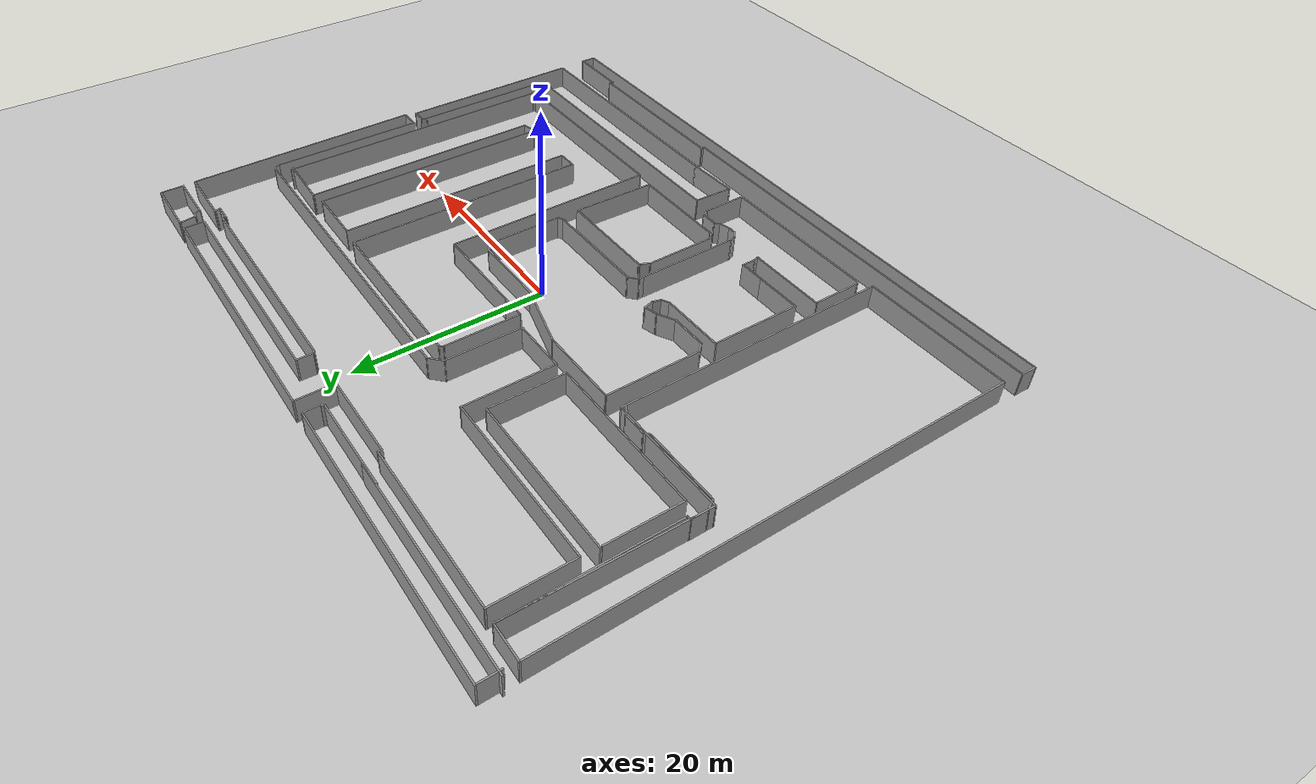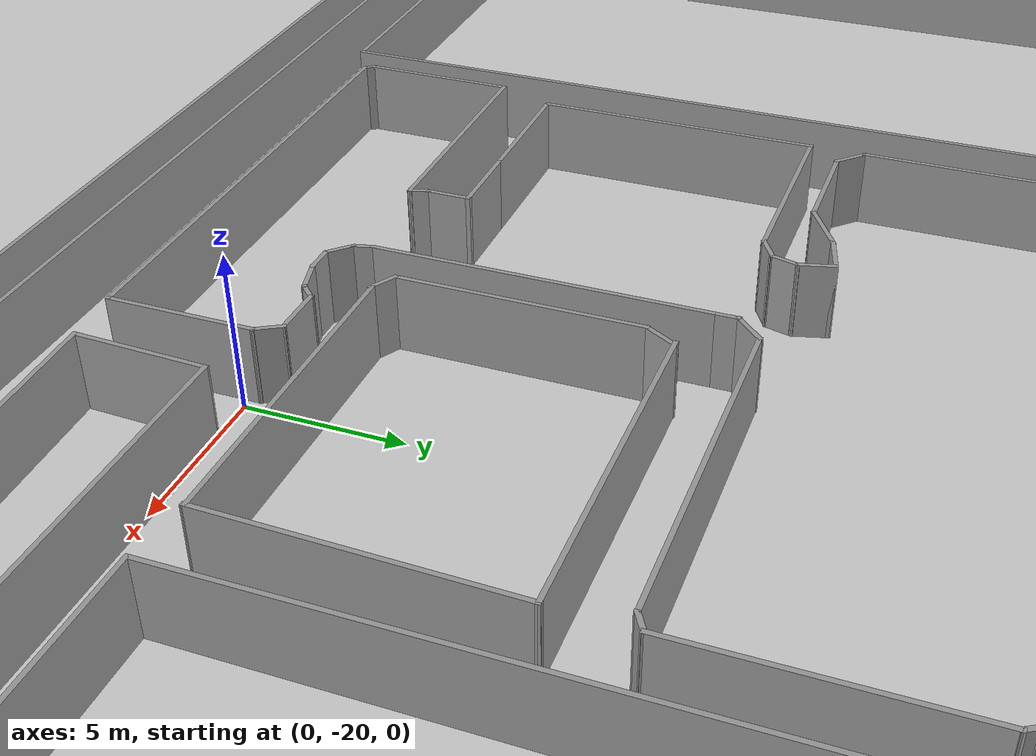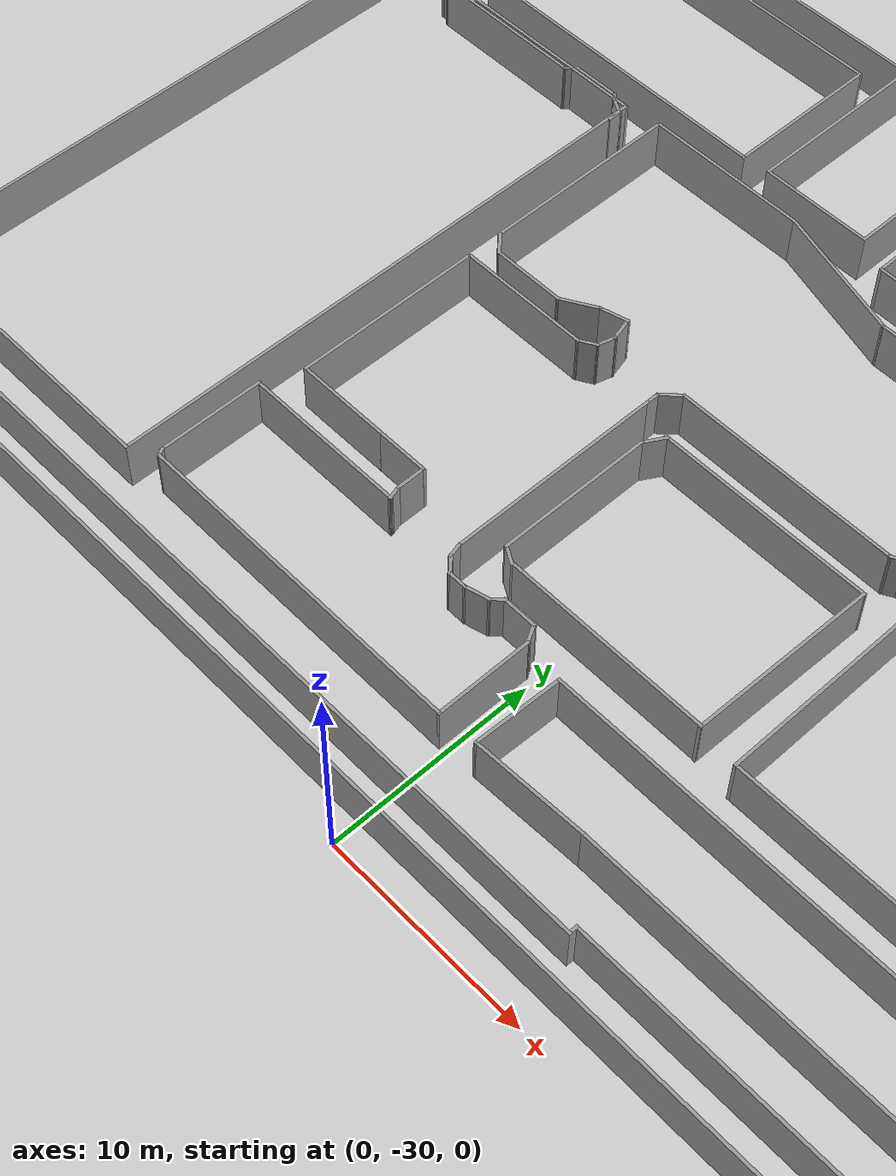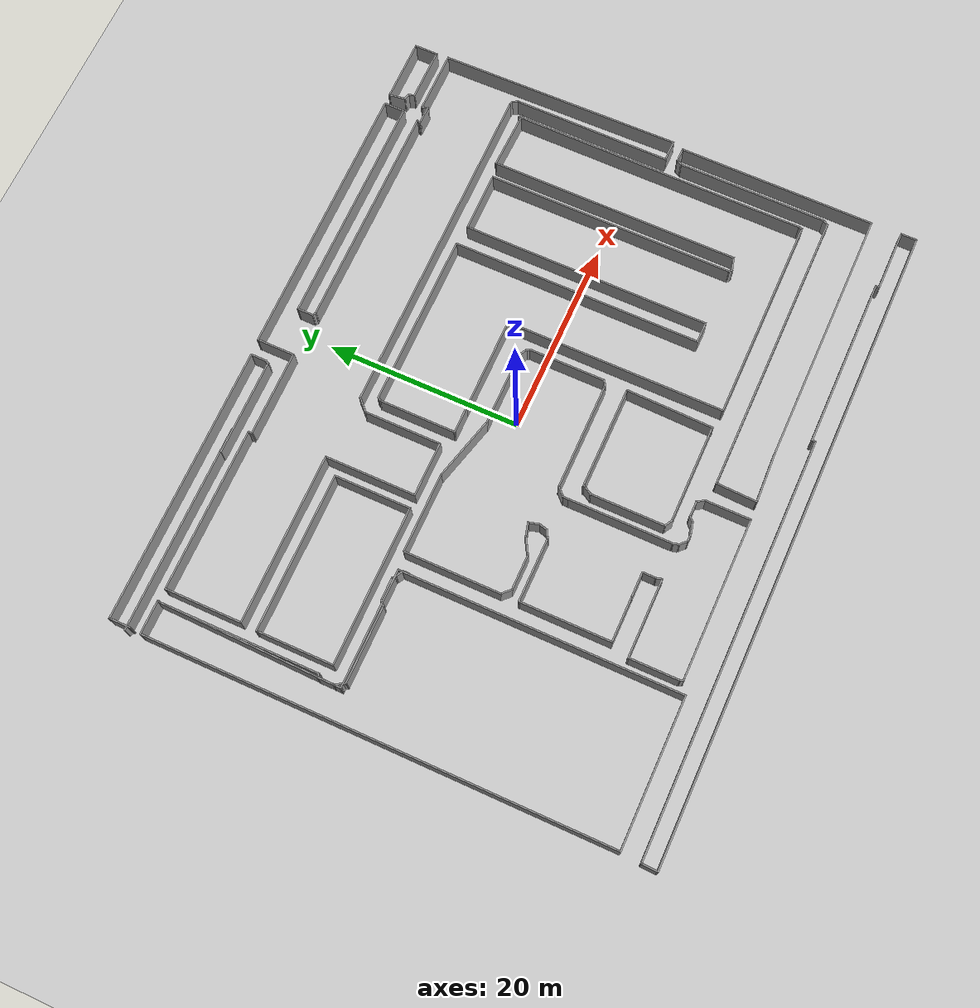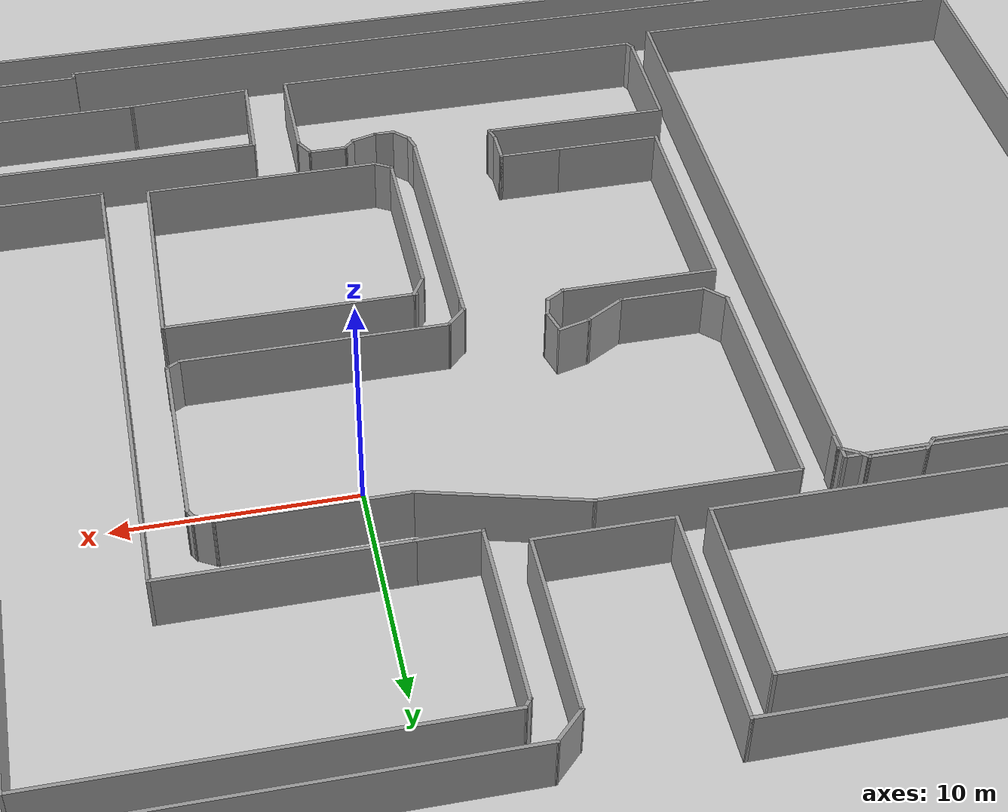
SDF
<sdf version="1.7">
 <world name="default">
  <light name="sun" type="directional">
   <pose>0 0 10 0 -0 0</pose>
   <diffuse>0.8 0.8 0.8 1</diffuse>
   <specular>0.2 0.2 0.2 1</specular>
   <attenuation>
    <range>1000</range>
    <constant>0.9</constant>
    <linear>0.01</linear>
    <quadratic>0.001</quadratic>
   </attenuation>
   <direction>-0.5 0.1 -0.9</direction>
   <spot><inner_angle>0</inner_angle><outer_angle>0</outer_angle><falloff>0</falloff></spot>
  </light>
  <model name="ground_plane">
   <static>1</static>
   <link name="link">
    <collision name="collision">
     <geometry><plane><normal>0 0 1</normal><size>100 100</size></plane></geometry>
     <surface><friction><ode><mu>100</mu><mu2>50</mu2></ode></friction></surface>
    </collision>
    <visual name="visual">
     <cast_shadows>0</cast_shadows>
     <geometry><plane><normal>0 0 1</normal><size>100 100</size></plane></geometry>
     <material>
      <script><uri>file://media/materials/scripts/gazebo.material</uri><name>Gazebo/Grey</name></script>
     </material>
    </visual>
   </link>
  </model>
  <gravity>0 0 -9.8</gravity>
  <magnetic_field>6e-06 2.3e-05 -4.2e-05</magnetic_field>
  <atmosphere type="adiabatic"/>
  <physics type="ode">
   <max_step_size>0.001</max_step_size>
   <real_time_factor>1</real_time_factor>
   <real_time_update_rate>1000</real_time_update_rate>
  </physics>
  <scene><ambient>0.4 0.4 0.4 1</ambient><background>0.7 0.7 0.7 1</background><shadows>1</shadows></scene>
  <audio><device>default</device></audio>
  <spherical_coordinates>
   <surface_model>EARTH_WGS84</surface_model>
   <latitude_deg>0</latitude_deg>
   <longitude_deg>0</longitude_deg>
   <elevation>0</elevation>
   <heading_deg>0</heading_deg>
  </spherical_coordinates>
  <model name="picture7">
   <pose>-0.026123 -1.16756 0 0 -0 0</pose>
   <link name="Wall_100">
    <collision name="Wall_100_Collision">
     <geometry><box><size>1.75 0.15 2.5</size></box></geometry>
     <pose>0 0 1.25 0 -0 0</pose>
    </collision>
    <visual name="Wall_100_Visual">
     <pose>0 0 1.25 0 -0 0</pose>
     <geometry><box><size>1.75 0.15 2.5</size></box></geometry>
     <material>
      <script><uri>file://media/materials/scripts/gazebo.material</uri><name>Gazebo/Grey</name></script>
      <ambient>1 1 1 1</ambient>
     </material>
     <meta><layer>0</layer></meta>
    </visual>
    <pose>33.2925 -26.6744 0 0 -0 1.5708</pose>
   </link>
   <link name="Wall_101">
    <collision name="Wall_101_Collision">
     <geometry><box><size>6.5 0.15 2.5</size></box></geometry>
     <pose>0 0 1.25 0 -0 0</pose>
    </collision>
    <visual name="Wall_101_Visual">
     <pose>0 0 1.25 0 -0 0</pose>
     <geometry><box><size>6.5 0.15 2.5</size></box></geometry>
     <material>
      <script><uri>file://media/materials/scripts/gazebo.material</uri><name>Gazebo/Grey</name></script>
      <ambient>1 1 1 1</ambient>
     </material>
     <meta><layer>0</layer></meta>
    </visual>
    <pose>30.1175 -25.8744 0 0 -0 3.14159</pose>
   </link>
   <link name="Wall_102">
    <collision name="Wall_102_Collision">
     <geometry><box><size>0.5 0.15 2.5</size></box></geometry>
     <pose>0 0 1.25 0 -0 0</pose>
    </collision>
    <visual name="Wall_102_Visual">
     <pose>0 0 1.25 0 -0 0</pose>
     <geometry><box><size>0.5 0.15 2.5</size></box></geometry>
     <material>
      <script><uri>file://media/materials/scripts/gazebo.material</uri><name>Gazebo/Grey</name></script>
      <ambient>1 1 1 1</ambient>
     </material>
     <meta><layer>0</layer></meta>
    </visual>
    <pose>26.9425 -25.6994 0 0 -0 1.5708</pose>
   </link>
   <link name="Wall_103">
    <collision name="Wall_103_Collision">
     <geometry><box><size>17.75 0.15 2.5</size></box></geometry>
     <pose>0 0 1.25 0 -0 0</pose>
    </collision>
    <visual name="Wall_103_Visual">
     <pose>0 0 1.25 0 -0 0</pose>
     <geometry><box><size>17.75 0.15 2.5</size></box></geometry>
     <material>
      <script><uri>file://media/materials/scripts/gazebo.material</uri><name>Gazebo/Grey</name></script>
      <ambient>1 1 1 1</ambient>
     </material>
     <meta><layer>0</layer></meta>
    </visual>
    <pose>18.1425 -25.5244 0 0 -0 3.14159</pose>
   </link>
   <link name="Wall_104">
    <collision name="Wall_104_Collision">
     <geometry><box><size>0.5 0.15 2.5</size></box></geometry>
     <pose>0 0 1.25 0 -0 0</pose>
    </collision>
    <visual name="Wall_104_Visual">
     <pose>0 0 1.25 0 -0 0</pose>
     <geometry><box><size>0.5 0.15 2.5</size></box></geometry>
     <material>
      <script><uri>file://media/materials/scripts/gazebo.material</uri><name>Gazebo/Grey</name></script>
      <ambient>1 1 1 1</ambient>
     </material>
     <meta><layer>0</layer></meta>
    </visual>
    <pose>9.34254 -25.6994 0 0 -0 -1.5708</pose>
   </link>
   <link name="Wall_105">
    <collision name="Wall_105_Collision">
     <geometry><box><size>43 0.15 2.5</size></box></geometry>
     <pose>0 0 1.25 0 -0 0</pose>
    </collision>
    <visual name="Wall_105_Visual">
     <pose>0 0 1.25 0 -0 0</pose>
     <geometry><box><size>43 0.15 2.5</size></box></geometry>
     <material>
      <script><uri>file://media/materials/scripts/gazebo.material</uri><name>Gazebo/Grey</name></script>
      <ambient>1 1 1 1</ambient>
     </material>
     <meta><layer>0</layer></meta>
    </visual>
    <pose>-12.0825 -25.8744 0 0 -0 3.14159</pose>
   </link>
   <link name="Wall_106">
    <collision name="Wall_106_Collision">
     <geometry><box><size>1.75078 0.15 2.5</size></box></geometry>
     <pose>0 0 1.25 0 -0 0</pose>
    </collision>
    <visual name="Wall_106_Visual">
     <pose>0 0 1.25 0 -0 0</pose>
     <geometry><box><size>1.75078 0.15 2.5</size></box></geometry>
     <material>
      <script><uri>file://media/materials/scripts/gazebo.material</uri><name>Gazebo/Grey</name></script>
      <ambient>1 1 1 1</ambient>
     </material>
     <meta><layer>0</layer></meta>
    </visual>
    <pose>-33.5325 -26.6744 0 0 -0 -1.60204</pose>
   </link>
   <link name="Wall_108">
    <collision name="Wall_108_Collision">
     <geometry><box><size>10 0.15 2.5</size></box></geometry>
     <pose>0 0 1.25 0 -0 0</pose>
    </collision>
    <visual name="Wall_108_Visual">
     <pose>0 0 1.25 0 -0 0</pose>
     <geometry><box><size>10 0.15 2.5</size></box></geometry>
     <material>
      <script><uri>file://media/materials/scripts/gazebo.material</uri><name>Gazebo/Grey</name></script>
      <ambient>1 1 1 1</ambient>
     </material>
     <meta><layer>0</layer></meta>
    </visual>
    <pose>-16.402 0.329792 0 0 -0 -1.5708</pose>
   </link>
   <link name="Wall_109">
    <collision name="Wall_109_Collision">
     <geometry><box><size>1.25 0.15 2.5</size></box></geometry>
     <pose>0 0 1.25 0 -0 0</pose>
    </collision>
    <visual name="Wall_109_Visual">
     <pose>0 0 1.25 0 -0 0</pose>
     <geometry><box><size>1.25 0.15 2.5</size></box></geometry>
     <material>
      <script><uri>file://media/materials/scripts/gazebo.material</uri><name>Gazebo/Grey</name></script>
      <ambient>1 1 1 1</ambient>
     </material>
     <meta><layer>0</layer></meta>
    </visual>
    <pose>-16.0131 -4.98412 0 0 -0 -0.785398</pose>
   </link>
   <link name="Wall_11">
    <collision name="Wall_11_Collision">
     <geometry><box><size>3.5 0.15 2.5</size></box></geometry>
     <pose>0 0 1.25 0 -0 0</pose>
    </collision>
    <visual name="Wall_11_Visual">
     <pose>0 0 1.25 0 -0 0</pose>
     <geometry><box><size>3.5 0.15 2.5</size></box></geometry>
     <material>
      <script><uri>file://media/materials/scripts/gazebo.material</uri><name>Gazebo/Grey</name></script>
      <ambient>1 1 1 1</ambient>
     </material>
     <meta><layer>0</layer></meta>
    </visual>
    <pose>-31.6293 24.0535 0 0 -0 0</pose>
   </link>
   <link name="Wall_110">
    <collision name="Wall_110_Collision">
     <geometry><box><size>3.75 0.15 2.5</size></box></geometry>
     <pose>0 0 1.25 0 -0 0</pose>
    </collision>
    <visual name="Wall_110_Visual">
     <pose>0 0 1.25 0 -0 0</pose>
     <geometry><box><size>3.75 0.15 2.5</size></box></geometry>
     <material>
      <script><uri>file://media/materials/scripts/gazebo.material</uri><name>Gazebo/Grey</name></script>
      <ambient>1 1 1 1</ambient>
     </material>
     <meta><layer>0</layer></meta>
    </visual>
    <pose>-13.8242 -5.37303 0 0 -0 0</pose>
   </link>
   <link name="Wall_111">
    <collision name="Wall_111_Collision">
     <geometry><box><size>2 0.15 2.5</size></box></geometry>
     <pose>0 0 1.25 0 -0 0</pose>
    </collision>
    <visual name="Wall_111_Visual">
     <pose>0 0 1.25 0 -0 0</pose>
     <geometry><box><size>2 0.15 2.5</size></box></geometry>
     <material>
      <script><uri>file://media/materials/scripts/gazebo.material</uri><name>Gazebo/Grey</name></script>
      <ambient>1 1 1 1</ambient>
     </material>
     <meta><layer>0</layer></meta>
    </visual>
    <pose>-11.2231 -4.91052 0 0 -0 0.523599</pose>
   </link>
   <link name="Wall_112">
    <collision name="Wall_112_Collision">
     <geometry><box><size>1.5 0.15 2.5</size></box></geometry>
     <pose>0 0 1.25 0 -0 0</pose>
    </collision>
    <visual name="Wall_112_Visual">
     <pose>0 0 1.25 0 -0 0</pose>
     <geometry><box><size>1.5 0.15 2.5</size></box></geometry>
     <material>
      <script><uri>file://media/materials/scripts/gazebo.material</uri><name>Gazebo/Grey</name></script>
      <ambient>1 1 1 1</ambient>
     </material>
     <meta><layer>0</layer></meta>
    </visual>
    <pose>-9.77003 -4.27332 0 0 -0 0.261799</pose>
   </link>
   <link name="Wall_113">
    <collision name="Wall_113_Collision">
     <geometry><box><size>1.25 0.15 2.5</size></box></geometry>
     <pose>0 0 1.25 0 -0 0</pose>
    </collision>
    <visual name="Wall_113_Visual">
     <pose>0 0 1.25 0 -0 0</pose>
     <geometry><box><size>1.25 0.15 2.5</size></box></geometry>
     <material>
      <script><uri>file://media/materials/scripts/gazebo.material</uri><name>Gazebo/Grey</name></script>
      <ambient>1 1 1 1</ambient>
     </material>
     <meta><layer>0</layer></meta>
    </visual>
    <pose>-8.97568 -4.62988 0 0 -0 -1.309</pose>
   </link>
   <link name="Wall_114">
    <collision name="Wall_114_Collision">
     <geometry><box><size>1 0.15 2.5</size></box></geometry>
     <pose>0 0 1.25 0 -0 0</pose>
    </collision>
    <visual name="Wall_114_Visual">
     <pose>0 0 1.25 0 -0 0</pose>
     <geometry><box><size>1 0.15 2.5</size></box></geometry>
     <material>
      <script><uri>file://media/materials/scripts/gazebo.material</uri><name>Gazebo/Grey</name></script>
      <ambient>1 1 1 1</ambient>
     </material>
     <meta><layer>0</layer></meta>
    </visual>
    <pose>-8.94332 -5.57166 0 0 -0 -1.8326</pose>
   </link>
   <link name="Wall_115">
    <collision name="Wall_115_Collision">
     <geometry><box><size>1 0.15 2.5</size></box></geometry>
     <pose>0 0 1.25 0 -0 0</pose>
    </collision>
    <visual name="Wall_115_Visual">
     <pose>0 0 1.25 0 -0 0</pose>
     <geometry><box><size>1 0.15 2.5</size></box></geometry>
     <material>
      <script><uri>file://media/materials/scripts/gazebo.material</uri><name>Gazebo/Grey</name></script>
      <ambient>1 1 1 1</ambient>
     </material>
     <meta><layer>0</layer></meta>
    </visual>
    <pose>-9.42139 -6.19467 0 0 -0 -2.61799</pose>
   </link>
   <link name="Wall_116">
    <collision name="Wall_116_Collision">
     <geometry><box><size>6.75 0.15 2.5</size></box></geometry>
     <pose>0 0 1.25 0 -0 0</pose>
    </collision>
    <visual name="Wall_116_Visual">
     <pose>0 0 1.25 0 -0 0</pose>
     <geometry><box><size>6.75 0.15 2.5</size></box></geometry>
     <material>
      <script><uri>file://media/materials/scripts/gazebo.material</uri><name>Gazebo/Grey</name></script>
      <ambient>1 1 1 1</ambient>
     </material>
     <meta><layer>0</layer></meta>
    </visual>
    <pose>-13.0894 -6.40717 0 0 -0 3.14159</pose>
   </link>
   <link name="Wall_117">
    <collision name="Wall_117_Collision">
     <geometry><box><size>9.5 0.15 2.5</size></box></geometry>
     <pose>0 0 1.25 0 -0 0</pose>
    </collision>
    <visual name="Wall_117_Visual">
     <pose>0 0 1.25 0 -0 0</pose>
     <geometry><box><size>9.5 0.15 2.5</size></box></geometry>
     <material>
      <script><uri>file://media/materials/scripts/gazebo.material</uri><name>Gazebo/Grey</name></script>
      <ambient>1 1 1 1</ambient>
     </material>
     <meta><layer>0</layer></meta>
    </visual>
    <pose>-16.3894 -11.0822 0 0 -0 -1.5708</pose>
   </link>
   <link name="Wall_118">
    <collision name="Wall_118_Collision">
     <geometry><box><size>4.75 0.15 2.5</size></box></geometry>
     <pose>0 0 1.25 0 -0 0</pose>
    </collision>
    <visual name="Wall_118_Visual">
     <pose>0 0 1.25 0 -0 0</pose>
     <geometry><box><size>4.75 0.15 2.5</size></box></geometry>
     <material>
      <script><uri>file://media/materials/scripts/gazebo.material</uri><name>Gazebo/Grey</name></script>
      <ambient>1 1 1 1</ambient>
     </material>
     <meta><layer>0</layer></meta>
    </visual>
    <pose>-14.0894 -15.7572 0 0 -0 0</pose>
   </link>
   <link name="Wall_119">
    <collision name="Wall_119_Collision">
     <geometry><box><size>2.75 0.15 2.5</size></box></geometry>
     <pose>0 0 1.25 0 -0 0</pose>
    </collision>
    <visual name="Wall_119_Visual">
     <pose>0 0 1.25 0 -0 0</pose>
     <geometry><box><size>2.75 0.15 2.5</size></box></geometry>
     <material>
      <script><uri>file://media/materials/scripts/gazebo.material</uri><name>Gazebo/Grey</name></script>
      <ambient>1 1 1 1</ambient>
     </material>
     <meta><layer>0</layer></meta>
    </visual>
    <pose>-10.4894 -15.7572 0 0 -0 0</pose>
   </link>
   <link name="Wall_12">
    <collision name="Wall_12_Collision">
     <geometry><box><size>0.25 0.15 2.5</size></box></geometry>
     <pose>0 0 1.25 0 -0 0</pose>
    </collision>
    <visual name="Wall_12_Visual">
     <pose>0 0 1.25 0 -0 0</pose>
     <geometry><box><size>0.25 0.15 2.5</size></box></geometry>
     <material>
      <script><uri>file://media/materials/scripts/gazebo.material</uri><name>Gazebo/Grey</name></script>
      <ambient>1 1 1 1</ambient>
     </material>
     <meta><layer>0</layer></meta>
    </visual>
    <pose>-29.911 24.0285 0 0 -0 -0.523599</pose>
   </link>
   <link name="Wall_120">
    <collision name="Wall_120_Collision">
     <geometry><box><size>1.5 0.15 2.5</size></box></geometry>
     <pose>0 0 1.25 0 -0 0</pose>
    </collision>
    <visual name="Wall_120_Visual">
     <pose>0 0 1.25 0 -0 0</pose>
     <geometry><box><size>1.5 0.15 2.5</size></box></geometry>
     <material>
      <script><uri>file://media/materials/scripts/gazebo.material</uri><name>Gazebo/Grey</name></script>
      <ambient>1 1 1 1</ambient>
     </material>
     <meta><layer>0</layer></meta>
    </visual>
    <pose>-9.18944 -16.4322 0 0 -0 -1.5708</pose>
   </link>
   <link name="Wall_121">
    <collision name="Wall_121_Collision">
     <geometry><box><size>0.75 0.15 2.5</size></box></geometry>
     <pose>0 0 1.25 0 -0 0</pose>
    </collision>
    <visual name="Wall_121_Visual">
     <pose>0 0 1.25 0 -0 0</pose>
     <geometry><box><size>0.75 0.15 2.5</size></box></geometry>
     <material>
      <script><uri>file://media/materials/scripts/gazebo.material</uri><name>Gazebo/Grey</name></script>
      <ambient>1 1 1 1</ambient>
     </material>
     <meta><layer>0</layer></meta>
    </visual>
    <pose>-9.1118 -17.397 0 0 -0 -1.309</pose>
   </link>
   <link name="Wall_122">
    <collision name="Wall_122_Collision">
     <geometry><box><size>8.25 0.15 2.5</size></box></geometry>
     <pose>0 0 1.25 0 -0 0</pose>
    </collision>
    <visual name="Wall_122_Visual">
     <pose>0 0 1.25 0 -0 0</pose>
     <geometry><box><size>8.25 0.15 2.5</size></box></geometry>
     <material>
      <script><uri>file://media/materials/scripts/gazebo.material</uri><name>Gazebo/Grey</name></script>
      <ambient>1 1 1 1</ambient>
     </material>
     <meta><layer>0</layer></meta>
    </visual>
    <pose>-13.0842 -17.6867 0 0 -0 3.14159</pose>
   </link>
   <link name="Wall_123">
    <collision name="Wall_123_Collision">
     <geometry><box><size>5.25 0.15 2.5</size></box></geometry>
     <pose>0 0 1.25 0 -0 0</pose>
    </collision>
    <visual name="Wall_123_Visual">
     <pose>0 0 1.25 0 -0 0</pose>
     <geometry><box><size>5.25 0.15 2.5</size></box></geometry>
     <material>
      <script><uri>file://media/materials/scripts/gazebo.material</uri><name>Gazebo/Grey</name></script>
      <ambient>1 1 1 1</ambient>
     </material>
     <meta><layer>0</layer></meta>
    </visual>
    <pose>-17.1342 -20.2367 0 0 -0 -1.5708</pose>
   </link>
   <link name="Wall_124">
    <collision name="Wall_124_Collision">
     <geometry><box><size>0.5 0.15 2.5</size></box></geometry>
     <pose>0 0 1.25 0 -0 0</pose>
    </collision>
    <visual name="Wall_124_Visual">
     <pose>0 0 1.25 0 -0 0</pose>
     <geometry><box><size>0.5 0.15 2.5</size></box></geometry>
     <material>
      <script><uri>file://media/materials/scripts/gazebo.material</uri><name>Gazebo/Grey</name></script>
      <ambient>1 1 1 1</ambient>
     </material>
     <meta><layer>0</layer></meta>
    </visual>
    <pose>-17.0467 -22.9383 0 0 -0 -1.0472</pose>
   </link>
   <link name="Wall_125">
    <collision name="Wall_125_Collision">
     <geometry><box><size>16.75 0.15 2.5</size></box></geometry>
     <pose>0 0 1.25 0 -0 0</pose>
    </collision>
    <visual name="Wall_125_Visual">
     <pose>0 0 1.25 0 -0 0</pose>
     <geometry><box><size>16.75 0.15 2.5</size></box></geometry>
     <material>
      <script><uri>file://media/materials/scripts/gazebo.material</uri><name>Gazebo/Grey</name></script>
      <ambient>1 1 1 1</ambient>
     </material>
     <meta><layer>0</layer></meta>
    </visual>
    <pose>-8.65915 -23.0898 0 0 -0 0</pose>
   </link>
   <link name="Wall_126">
    <collision name="Wall_126_Collision">
     <geometry><box><size>4.75 0.15 2.5</size></box></geometry>
     <pose>0 0 1.25 0 -0 0</pose>
    </collision>
    <visual name="Wall_126_Visual">
     <pose>0 0 1.25 0 -0 0</pose>
     <geometry><box><size>4.75 0.15 2.5</size></box></geometry>
     <material>
      <script><uri>file://media/materials/scripts/gazebo.material</uri><name>Gazebo/Grey</name></script>
      <ambient>1 1 1 1</ambient>
     </material>
     <meta><layer>0</layer></meta>
    </visual>
    <pose>-0.359154 -20.7898 0 0 -0 1.5708</pose>
   </link>
   <link name="Wall_127">
    <collision name="Wall_127_Collision">
     <geometry><box><size>1 0.15 2.5</size></box></geometry>
     <pose>0 0 1.25 0 -0 0</pose>
    </collision>
    <visual name="Wall_127_Visual">
     <pose>0 0 1.25 0 -0 0</pose>
     <geometry><box><size>1 0.15 2.5</size></box></geometry>
     <material>
      <script><uri>file://media/materials/scripts/gazebo.material</uri><name>Gazebo/Grey</name></script>
      <ambient>1 1 1 1</ambient>
     </material>
     <meta><layer>0</layer></meta>
    </visual>
    <pose>-0.571654 -18.1218 0 0 -0 2.0944</pose>
   </link>
   <link name="Wall_128">
    <collision name="Wall_128_Collision">
     <geometry><box><size>1.75 0.15 2.5</size></box></geometry>
     <pose>0 0 1.25 0 -0 0</pose>
    </collision>
    <visual name="Wall_128_Visual">
     <pose>0 0 1.25 0 -0 0</pose>
     <geometry><box><size>1.75 0.15 2.5</size></box></geometry>
     <material>
      <script><uri>file://media/materials/scripts/gazebo.material</uri><name>Gazebo/Grey</name></script>
      <ambient>1 1 1 1</ambient>
     </material>
     <meta><layer>0</layer></meta>
    </visual>
    <pose>-1.58415 -17.7537 0 0 -0 3.14159</pose>
   </link>
   <link name="Wall_129">
    <collision name="Wall_129_Collision">
     <geometry><box><size>0.75 0.15 2.5</size></box></geometry>
     <pose>0 0 1.25 0 -0 0</pose>
    </collision>
    <visual name="Wall_129_Visual">
     <pose>0 0 1.25 0 -0 0</pose>
     <geometry><box><size>0.75 0.15 2.5</size></box></geometry>
     <material>
      <script><uri>file://media/materials/scripts/gazebo.material</uri><name>Gazebo/Grey</name></script>
      <ambient>1 1 1 1</ambient>
     </material>
     <meta><layer>0</layer></meta>
    </visual>
    <pose>-2.59629 -17.9658 0 0 -0 -2.35619</pose>
   </link>
   <link name="Wall_130">
    <collision name="Wall_130_Collision">
     <geometry><box><size>1.25 0.15 2.5</size></box></geometry>
     <pose>0 0 1.25 0 -0 0</pose>
    </collision>
    <visual name="Wall_130_Visual">
     <pose>0 0 1.25 0 -0 0</pose>
     <geometry><box><size>1.25 0.15 2.5</size></box></geometry>
     <material>
      <script><uri>file://media/materials/scripts/gazebo.material</uri><name>Gazebo/Grey</name></script>
      <ambient>1 1 1 1</ambient>
     </material>
     <meta><layer>0</layer></meta>
    </visual>
    <pose>-3.33968 -18.3203 0 0 -0 -2.87979</pose>
   </link>
   <link name="Wall_131">
    <collision name="Wall_131_Collision">
     <geometry><box><size>1 0.15 2.5</size></box></geometry>
     <pose>0 0 1.25 0 -0 0</pose>
    </collision>
    <visual name="Wall_131_Visual">
     <pose>0 0 1.25 0 -0 0</pose>
     <geometry><box><size>1 0.15 2.5</size></box></geometry>
     <material>
      <script><uri>file://media/materials/scripts/gazebo.material</uri><name>Gazebo/Grey</name></script>
      <ambient>1 1 1 1</ambient>
     </material>
     <meta><layer>0</layer></meta>
    </visual>
    <pose>-4.29594 -18.4627 0 0 -0 3.14159</pose>
   </link>
   <link name="Wall_132">
    <collision name="Wall_132_Collision">
     <geometry><box><size>1 0.15 2.5</size></box></geometry>
     <pose>0 0 1.25 0 -0 0</pose>
    </collision>
    <visual name="Wall_132_Visual">
     <pose>0 0 1.25 0 -0 0</pose>
     <geometry><box><size>1 0.15 2.5</size></box></geometry>
     <material>
      <script><uri>file://media/materials/scripts/gazebo.material</uri><name>Gazebo/Grey</name></script>
      <ambient>1 1 1 1</ambient>
     </material>
     <meta><layer>0</layer></meta>
    </visual>
    <pose>-5.02146 -18.1622 0 0 -0 2.35619</pose>
   </link>
   <link name="Wall_133">
    <collision name="Wall_133_Collision">
     <geometry><box><size>0.75 0.15 2.5</size></box></geometry>
     <pose>0 0 1.25 0 -0 0</pose>
    </collision>
    <visual name="Wall_133_Visual">
     <pose>0 0 1.25 0 -0 0</pose>
     <geometry><box><size>0.75 0.15 2.5</size></box></geometry>
     <material>
      <script><uri>file://media/materials/scripts/gazebo.material</uri><name>Gazebo/Grey</name></script>
      <ambient>1 1 1 1</ambient>
     </material>
     <meta><layer>0</layer></meta>
    </visual>
    <pose>-5.39962 -17.5719 0 0 -0 1.8326</pose>
   </link>
   <link name="Wall_134">
    <collision name="Wall_134_Collision">
     <geometry><box><size>10.75 0.15 2.5</size></box></geometry>
     <pose>0 0 1.25 0 -0 0</pose>
    </collision>
    <visual name="Wall_134_Visual">
     <pose>0 0 1.25 0 -0 0</pose>
     <geometry><box><size>10.75 0.15 2.5</size></box></geometry>
     <material>
      <script><uri>file://media/materials/scripts/gazebo.material</uri><name>Gazebo/Grey</name></script>
      <ambient>1 1 1 1</ambient>
     </material>
     <meta><layer>0</layer></meta>
    </visual>
    <pose>-5.47727 -11.9821 0 0 -0 1.5708</pose>
   </link>
   <link name="Wall_135">
    <collision name="Wall_135_Collision">
     <geometry><box><size>0.75 0.15 2.5</size></box></geometry>
     <pose>0 0 1.25 0 -0 0</pose>
    </collision>
    <visual name="Wall_135_Visual">
     <pose>0 0 1.25 0 -0 0</pose>
     <geometry><box><size>0.75 0.15 2.5</size></box></geometry>
     <material>
      <script><uri>file://media/materials/scripts/gazebo.material</uri><name>Gazebo/Grey</name></script>
      <ambient>1 1 1 1</ambient>
     </material>
     <meta><layer>0</layer></meta>
    </visual>
    <pose>-5.47727 -6.38209 0 0 -0 1.5708</pose>
   </link>
   <link name="Wall_136">
    <collision name="Wall_136_Collision">
     <geometry><box><size>1.25 0.15 2.5</size></box></geometry>
     <pose>0 0 1.25 0 -0 0</pose>
    </collision>
    <visual name="Wall_136_Visual">
     <pose>0 0 1.25 0 -0 0</pose>
     <geometry><box><size>1.25 0.15 2.5</size></box></geometry>
     <material>
      <script><uri>file://media/materials/scripts/gazebo.material</uri><name>Gazebo/Grey</name></script>
      <ambient>1 1 1 1</ambient>
     </material>
     <meta><layer>0</layer></meta>
    </visual>
    <pose>-5.08836 -5.69318 0 0 -0 0.785398</pose>
   </link>
   <link name="Wall_137">
    <collision name="Wall_137_Collision">
     <geometry><box><size>11.25 0.15 2.5</size></box></geometry>
     <pose>0 0 1.25 0 -0 0</pose>
    </collision>
    <visual name="Wall_137_Visual">
     <pose>0 0 1.25 0 -0 0</pose>
     <geometry><box><size>11.25 0.15 2.5</size></box></geometry>
     <material>
      <script><uri>file://media/materials/scripts/gazebo.material</uri><name>Gazebo/Grey</name></script>
      <ambient>1 1 1 1</ambient>
     </material>
     <meta><layer>0</layer></meta>
    </visual>
    <pose>0.850549 -5.30427 0 0 -0 0</pose>
   </link>
   <link name="Wall_138">
    <collision name="Wall_138_Collision">
     <geometry><box><size>0.75 0.15 2.5</size></box></geometry>
     <pose>0 0 1.25 0 -0 0</pose>
    </collision>
    <visual name="Wall_138_Visual">
     <pose>0 0 1.25 0 -0 0</pose>
     <geometry><box><size>0.75 0.15 2.5</size></box></geometry>
     <material>
      <script><uri>file://media/materials/scripts/gazebo.material</uri><name>Gazebo/Grey</name></script>
      <ambient>1 1 1 1</ambient>
     </material>
     <meta><layer>0</layer></meta>
    </visual>
    <pose>6.66036 -5.15427 0 0 -0 0.523599</pose>
   </link>
   <link name="Wall_139">
    <collision name="Wall_139_Collision">
     <geometry><box><size>8 0.15 2.5</size></box></geometry>
     <pose>0 0 1.25 0 -0 0</pose>
    </collision>
    <visual name="Wall_139_Visual">
     <pose>0 0 1.25 0 -0 0</pose>
     <geometry><box><size>8 0.15 2.5</size></box></geometry>
     <material>
      <script><uri>file://media/materials/scripts/gazebo.material</uri><name>Gazebo/Grey</name></script>
      <ambient>1 1 1 1</ambient>
     </material>
     <meta><layer>0</layer></meta>
    </visual>
    <pose>6.92016 -1.07927 0 0 -0 1.5708</pose>
   </link>
   <link name="Wall_140">
    <collision name="Wall_140_Collision">
     <geometry><box><size>0.5 0.15 2.5</size></box></geometry>
     <pose>0 0 1.25 0 -0 0</pose>
    </collision>
    <visual name="Wall_140_Visual">
     <pose>0 0 1.25 0 -0 0</pose>
     <geometry><box><size>0.5 0.15 2.5</size></box></geometry>
     <material>
      <script><uri>file://media/materials/scripts/gazebo.material</uri><name>Gazebo/Grey</name></script>
      <ambient>1 1 1 1</ambient>
     </material>
     <meta><layer>0</layer></meta>
    </visual>
    <pose>6.83266 2.99729 0 0 -0 2.0944</pose>
   </link>
   <link name="Wall_141">
    <collision name="Wall_141_Collision">
     <geometry><box><size>1 0.15 2.5</size></box></geometry>
     <pose>0 0 1.25 0 -0 0</pose>
    </collision>
    <visual name="Wall_141_Visual">
     <pose>0 0 1.25 0 -0 0</pose>
     <geometry><box><size>1 0.15 2.5</size></box></geometry>
     <material>
      <script><uri>file://media/materials/scripts/gazebo.material</uri><name>Gazebo/Grey</name></script>
      <ambient>1 1 1 1</ambient>
     </material>
     <meta><layer>0</layer></meta>
    </visual>
    <pose>6.3771 3.36134 0 0 -0 2.61799</pose>
   </link>
   <link name="Wall_142">
    <collision name="Wall_142_Collision">
     <geometry><box><size>7.75 0.15 2.5</size></box></geometry>
     <pose>0 0 1.25 0 -0 0</pose>
    </collision>
    <visual name="Wall_142_Visual">
     <pose>0 0 1.25 0 -0 0</pose>
     <geometry><box><size>7.75 0.15 2.5</size></box></geometry>
     <material>
      <script><uri>file://media/materials/scripts/gazebo.material</uri><name>Gazebo/Grey</name></script>
      <ambient>1 1 1 1</ambient>
     </material>
     <meta><layer>0</layer></meta>
    </visual>
    <pose>2.20904 3.57384 0 0 -0 3.14159</pose>
   </link>
   <link name="Wall_143">
    <collision name="Wall_143_Collision">
     <geometry><box><size>7 0.15 2.5</size></box></geometry>
     <pose>0 0 1.25 0 -0 0</pose>
    </collision>
    <visual name="Wall_143_Visual">
     <pose>0 0 1.25 0 -0 0</pose>
     <geometry><box><size>7 0.15 2.5</size></box></geometry>
     <material>
      <script><uri>file://media/materials/scripts/gazebo.material</uri><name>Gazebo/Grey</name></script>
      <ambient>1 1 1 1</ambient>
     </material>
     <meta><layer>0</layer></meta>
    </visual>
    <pose>-4.89925 4.4603 0 0 -0 2.87979</pose>
   </link>
   <link name="Wall_144">
    <collision name="Wall_144_Collision">
     <geometry><box><size>8.25 0.15 2.5</size></box></geometry>
     <pose>0 0 1.25 0 -0 0</pose>
    </collision>
    <visual name="Wall_144_Visual">
     <pose>0 0 1.25 0 -0 0</pose>
     <geometry><box><size>8.25 0.15 2.5</size></box></geometry>
     <material>
      <script><uri>file://media/materials/scripts/gazebo.material</uri><name>Gazebo/Grey</name></script>
      <ambient>1 1 1 1</ambient>
     </material>
     <meta><layer>0</layer></meta>
    </visual>
    <pose>-12.2575 5.34675 0 0 -0 3.14159</pose>
   </link>
   <link name="Wall_146">
    <collision name="Wall_146_Collision">
     <geometry><box><size>1.25 0.15 2.5</size></box></geometry>
     <pose>0 0 1.25 0 -0 0</pose>
    </collision>
    <visual name="Wall_146_Visual">
     <pose>0 0 1.25 0 -0 0</pose>
     <geometry><box><size>1.25 0.15 2.5</size></box></geometry>
     <material>
      <script><uri>file://media/materials/scripts/gazebo.material</uri><name>Gazebo/Grey</name></script>
      <ambient>1 1 1 1</ambient>
     </material>
     <meta><layer>0</layer></meta>
    </visual>
    <pose>-3.90164 -7.8752 0 0 -0 -2.0944</pose>
   </link>
   <link name="Wall_147">
    <collision name="Wall_147_Collision">
     <geometry><box><size>7.75 0.15 2.5</size></box></geometry>
     <pose>0 0 1.25 0 -0 0</pose>
    </collision>
    <visual name="Wall_147_Visual">
     <pose>0 0 1.25 0 -0 0</pose>
     <geometry><box><size>7.75 0.15 2.5</size></box></geometry>
     <material>
      <script><uri>file://media/materials/scripts/gazebo.material</uri><name>Gazebo/Grey</name></script>
      <ambient>1 1 1 1</ambient>
     </material>
     <meta><layer>0</layer></meta>
    </visual>
    <pose>-4.17664 -12.1515 0 0 -0 -1.5708</pose>
   </link>
   <link name="Wall_148">
    <collision name="Wall_148_Collision">
     <geometry><box><size>1.01812 0.15 2.5</size></box></geometry>
     <pose>0 0 1.25 0 -0 0</pose>
    </collision>
    <visual name="Wall_148_Visual">
     <pose>0 0 1.25 0 -0 0</pose>
     <geometry><box><size>1.01812 0.15 2.5</size></box></geometry>
     <material>
      <script><uri>file://media/materials/scripts/gazebo.material</uri><name>Gazebo/Grey</name></script>
      <ambient>1 1 1 1</ambient>
     </material>
     <meta><layer>0</layer></meta>
    </visual>
    <pose>-3.79976 -16.1669 0 0 -0 -0.519105</pose>
   </link>
   <link name="Wall_149">
    <collision name="Wall_149_Collision">
     <geometry><box><size>10.25 0.15 2.5</size></box></geometry>
     <pose>0 0 1.25 0 -0 0</pose>
    </collision>
    <visual name="Wall_149_Visual">
     <pose>0 0 1.25 0 -0 0</pose>
     <geometry><box><size>10.25 0.15 2.5</size></box></geometry>
     <material>
      <script><uri>file://media/materials/scripts/gazebo.material</uri><name>Gazebo/Grey</name></script>
      <ambient>1 1 1 1</ambient>
     </material>
     <meta><layer>0</layer></meta>
    </visual>
    <pose>1.62712 -16.3424 0 0 -0 0</pose>
   </link>
   <link name="Wall_15">
    <collision name="Wall_15_Collision">
     <geometry><box><size>16.75 0.15 2.5</size></box></geometry>
     <pose>0 0 1.25 0 -0 0</pose>
    </collision>
    <visual name="Wall_15_Visual">
     <pose>0 0 1.25 0 -0 0</pose>
     <geometry><box><size>16.75 0.15 2.5</size></box></geometry>
     <material>
      <script><uri>file://media/materials/scripts/gazebo.material</uri><name>Gazebo/Grey</name></script>
      <ambient>1 1 1 1</ambient>
     </material>
     <meta><layer>0</layer></meta>
    </visual>
    <pose>-29.9543 15.7535 0 0 -0 -1.5708</pose>
   </link>
   <link name="Wall_150">
    <collision name="Wall_150_Collision">
     <geometry><box><size>9.13288 0.15 2.5</size></box></geometry>
     <pose>0 0 1.25 0 -0 0</pose>
    </collision>
    <visual name="Wall_150_Visual">
     <pose>0 0 1.25 0 -0 0</pose>
     <geometry><box><size>9.13288 0.15 2.5</size></box></geometry>
     <material>
      <script><uri>file://media/materials/scripts/gazebo.material</uri><name>Gazebo/Grey</name></script>
      <ambient>1 1 1 1</ambient>
     </material>
     <meta><layer>0</layer></meta>
    </visual>
    <pose>6.77655 -11.8919 0 0 -0 1.54866</pose>
   </link>
   <link name="Wall_151">
    <collision name="Wall_151_Collision">
     <geometry><box><size>10.75 0.15 2.5</size></box></geometry>
     <pose>0 0 1.25 0 -0 0</pose>
    </collision>
    <visual name="Wall_151_Visual">
     <pose>0 0 1.25 0 -0 0</pose>
     <geometry><box><size>10.75 0.15 2.5</size></box></geometry>
     <material>
      <script><uri>file://media/materials/scripts/gazebo.material</uri><name>Gazebo/Grey</name></script>
      <ambient>1 1 1 1</ambient>
     </material>
     <meta><layer>0</layer></meta>
    </visual>
    <pose>1.57598 -7.40151 0 0 -0 3.14159</pose>
   </link>
   <link name="Wall_156">
    <collision name="Wall_156_Collision">
     <geometry><box><size>5.50418 0.15 2.5</size></box></geometry>
     <pose>0 0 1.25 0 -0 0</pose>
    </collision>
    <visual name="Wall_156_Visual">
     <pose>0 0 1.25 0 -0 0</pose>
     <geometry><box><size>5.50418 0.15 2.5</size></box></geometry>
     <material>
      <script><uri>file://media/materials/scripts/gazebo.material</uri><name>Gazebo/Grey</name></script>
      <ambient>1 1 1 1</ambient>
     </material>
     <meta><layer>0</layer></meta>
    </visual>
    <pose>4.17479 -22.8521 0 0 -0 0.039531</pose>
   </link>
   <link name="Wall_157">
    <collision name="Wall_157_Collision">
     <geometry><box><size>26.5 0.15 2.5</size></box></geometry>
     <pose>0 0 1.25 0 -0 0</pose>
    </collision>
    <visual name="Wall_157_Visual">
     <pose>0 0 1.25 0 -0 0</pose>
     <geometry><box><size>26.5 0.15 2.5</size></box></geometry>
     <material>
      <script><uri>file://media/materials/scripts/gazebo.material</uri><name>Gazebo/Grey</name></script>
      <ambient>1 1 1 1</ambient>
     </material>
     <meta><layer>0</layer></meta>
    </visual>
    <pose>20.0248 -22.7463 0 0 -0 0</pose>
   </link>
   <link name="Wall_158">
    <collision name="Wall_158_Collision">
     <geometry><box><size>20.5 0.15 2.5</size></box></geometry>
     <pose>0 0 1.25 0 -0 0</pose>
    </collision>
    <visual name="Wall_158_Visual">
     <pose>0 0 1.25 0 -0 0</pose>
     <geometry><box><size>20.5 0.15 2.5</size></box></geometry>
     <material>
      <script><uri>file://media/materials/scripts/gazebo.material</uri><name>Gazebo/Grey</name></script>
      <ambient>1 1 1 1</ambient>
     </material>
     <meta><layer>0</layer></meta>
    </visual>
    <pose>33.1998 -12.5713 0 0 -0 1.5708</pose>
   </link>
   <link name="Wall_159">
    <collision name="Wall_159_Collision">
     <geometry><box><size>1.5 0.15 2.5</size></box></geometry>
     <pose>0 0 1.25 0 -0 0</pose>
    </collision>
    <visual name="Wall_159_Visual">
     <pose>0 0 1.25 0 -0 0</pose>
     <geometry><box><size>1.5 0.15 2.5</size></box></geometry>
     <material>
      <script><uri>file://media/materials/scripts/gazebo.material</uri><name>Gazebo/Grey</name></script>
      <ambient>1 1 1 1</ambient>
     </material>
     <meta><layer>0</layer></meta>
    </visual>
    <pose>32.5248 -2.39634 0 0 -0 3.14159</pose>
   </link>
   <link name="Wall_16">
    <collision name="Wall_16_Collision">
     <geometry><box><size>0.5 0.15 2.5</size></box></geometry>
     <pose>0 0 1.25 0 -0 0</pose>
    </collision>
    <visual name="Wall_16_Visual">
     <pose>0 0 1.25 0 -0 0</pose>
     <geometry><box><size>0.5 0.15 2.5</size></box></geometry>
     <material>
      <script><uri>file://media/materials/scripts/gazebo.material</uri><name>Gazebo/Grey</name></script>
      <ambient>1 1 1 1</ambient>
     </material>
     <meta><layer>0</layer></meta>
    </visual>
    <pose>-30.1233 7.40825 0 0 -0 -2.87979</pose>
   </link>
   <link name="Wall_160">
    <collision name="Wall_160_Collision">
     <geometry><box><size>0.75 0.15 2.5</size></box></geometry>
     <pose>0 0 1.25 0 -0 0</pose>
    </collision>
    <visual name="Wall_160_Visual">
     <pose>0 0 1.25 0 -0 0</pose>
     <geometry><box><size>0.75 0.15 2.5</size></box></geometry>
     <material>
      <script><uri>file://media/materials/scripts/gazebo.material</uri><name>Gazebo/Grey</name></script>
      <ambient>1 1 1 1</ambient>
     </material>
     <meta><layer>0</layer></meta>
    </visual>
    <pose>31.6998 -2.65615 0 0 -0 -2.0944</pose>
   </link>
   <link name="Wall_161">
    <collision name="Wall_161_Collision">
     <geometry><box><size>15.5 0.15 2.5</size></box></geometry>
     <pose>0 0 1.25 0 -0 0</pose>
    </collision>
    <visual name="Wall_161_Visual">
     <pose>0 0 1.25 0 -0 0</pose>
     <geometry><box><size>15.5 0.15 2.5</size></box></geometry>
     <material>
      <script><uri>file://media/materials/scripts/gazebo.material</uri><name>Gazebo/Grey</name></script>
      <ambient>1 1 1 1</ambient>
     </material>
     <meta><layer>0</layer></meta>
    </visual>
    <pose>31.5498 -10.591 0 0 -0 -1.5708</pose>
   </link>
   <link name="Wall_162">
    <collision name="Wall_162_Collision">
     <geometry><box><size>0.75 0.15 2.5</size></box></geometry>
     <pose>0 0 1.25 0 -0 0</pose>
    </collision>
    <visual name="Wall_162_Visual">
     <pose>0 0 1.25 0 -0 0</pose>
     <geometry><box><size>0.75 0.15 2.5</size></box></geometry>
     <material>
      <script><uri>file://media/materials/scripts/gazebo.material</uri><name>Gazebo/Grey</name></script>
      <ambient>1 1 1 1</ambient>
     </material>
     <meta><layer>0</layer></meta>
    </visual>
    <pose>31.3998 -18.5258 0 0 -0 -2.0944</pose>
   </link>
   <link name="Wall_163">
    <collision name="Wall_163_Collision">
     <geometry><box><size>29.75 0.15 2.5</size></box></geometry>
     <pose>0 0 1.25 0 -0 0</pose>
    </collision>
    <visual name="Wall_163_Visual">
     <pose>0 0 1.25 0 -0 0</pose>
     <geometry><box><size>29.75 0.15 2.5</size></box></geometry>
     <material>
      <script><uri>file://media/materials/scripts/gazebo.material</uri><name>Gazebo/Grey</name></script>
      <ambient>1 1 1 1</ambient>
     </material>
     <meta><layer>0</layer></meta>
    </visual>
    <pose>16.4498 -18.7856 0 0 -0 3.14159</pose>
   </link>
   <link name="Wall_166">
    <collision name="Wall_166_Collision">
     <geometry><box><size>4.32507 0.15 2.5</size></box></geometry>
     <pose>0 0 1.25 0 -0 0</pose>
    </collision>
    <visual name="Wall_166_Visual">
     <pose>0 0 1.25 0 -0 0</pose>
     <geometry><box><size>4.32507 0.15 2.5</size></box></geometry>
     <material>
      <script><uri>file://media/materials/scripts/gazebo.material</uri><name>Gazebo/Grey</name></script>
      <ambient>1 1 1 1</ambient>
     </material>
     <meta><layer>0</layer></meta>
    </visual>
    <pose>1.57479 -20.8718 0 0 -0 1.53486</pose>
   </link>
   <link name="Wall_17">
    <collision name="Wall_17_Collision">
     <geometry><box><size>1.75 0.15 2.5</size></box></geometry>
     <pose>0 0 1.25 0 -0 0</pose>
    </collision>
    <visual name="Wall_17_Visual">
     <pose>0 0 1.25 0 -0 0</pose>
     <geometry><box><size>1.75 0.15 2.5</size></box></geometry>
     <material>
      <script><uri>file://media/materials/scripts/gazebo.material</uri><name>Gazebo/Grey</name></script>
      <ambient>1 1 1 1</ambient>
     </material>
     <meta><layer>0</layer></meta>
    </visual>
    <pose>-30.2924 6.56296 0 0 -0 -1.5708</pose>
   </link>
   <link name="Wall_18">
    <collision name="Wall_18_Collision">
     <geometry><box><size>1.25 0.15 2.5</size></box></geometry>
     <pose>0 0 1.25 0 -0 0</pose>
    </collision>
    <visual name="Wall_18_Visual">
     <pose>0 0 1.25 0 -0 0</pose>
     <geometry><box><size>1.25 0.15 2.5</size></box></geometry>
     <material>
      <script><uri>file://media/materials/scripts/gazebo.material</uri><name>Gazebo/Grey</name></script>
      <ambient>1 1 1 1</ambient>
     </material>
     <meta><layer>0</layer></meta>
    </visual>
    <pose>-30.0174 5.28665 0 0 -0 -1.0472</pose>
   </link>
   <link name="Wall_19">
    <collision name="Wall_19_Collision">
     <geometry><box><size>8 0.15 2.5</size></box></geometry>
     <pose>0 0 1.25 0 -0 0</pose>
    </collision>
    <visual name="Wall_19_Visual">
     <pose>0 0 1.25 0 -0 0</pose>
     <geometry><box><size>8 0.15 2.5</size></box></geometry>
     <material>
      <script><uri>file://media/materials/scripts/gazebo.material</uri><name>Gazebo/Grey</name></script>
      <ambient>1 1 1 1</ambient>
     </material>
     <meta><layer>0</layer></meta>
    </visual>
    <pose>-25.8174 4.81033 0 0 -0 0</pose>
   </link>
   <link name="Wall_20">
    <collision name="Wall_20_Collision">
     <geometry><box><size>0.75 0.15 2.5</size></box></geometry>
     <pose>0 0 1.25 0 -0 0</pose>
    </collision>
    <visual name="Wall_20_Visual">
     <pose>0 0 1.25 0 -0 0</pose>
     <geometry><box><size>0.75 0.15 2.5</size></box></geometry>
     <material>
      <script><uri>file://media/materials/scripts/gazebo.material</uri><name>Gazebo/Grey</name></script>
      <ambient>1 1 1 1</ambient>
     </material>
     <meta><layer>0</layer></meta>
    </visual>
    <pose>-21.6802 5.02246 0 0 -0 0.785398</pose>
   </link>
   <link name="Wall_21">
    <collision name="Wall_21_Collision">
     <geometry><box><size>2.5 0.15 2.5</size></box></geometry>
     <pose>0 0 1.25 0 -0 0</pose>
    </collision>
    <visual name="Wall_21_Visual">
     <pose>0 0 1.25 0 -0 0</pose>
     <geometry><box><size>2.5 0.15 2.5</size></box></geometry>
     <material>
      <script><uri>file://media/materials/scripts/gazebo.material</uri><name>Gazebo/Grey</name></script>
      <ambient>1 1 1 1</ambient>
     </material>
     <meta><layer>0</layer></meta>
    </visual>
    <pose>-20.2931 5.2346 0 0 -0 0</pose>
   </link>
   <link name="Wall_22">
    <collision name="Wall_22_Collision">
     <geometry><box><size>0.15 0.15 2.5</size></box></geometry>
     <pose>0 0 1.25 0 -0 0</pose>
    </collision>
    <visual name="Wall_22_Visual">
     <pose>0 0 1.25 0 -0 0</pose>
     <geometry><box><size>0.15 0.15 2.5</size></box></geometry>
     <material>
      <script><uri>file://media/materials/scripts/gazebo.material</uri><name>Gazebo/Grey</name></script>
      <ambient>1 1 1 1</ambient>
     </material>
     <meta><layer>0</layer></meta>
    </visual>
    <pose>-19.1181 5.2346 0 0 -0 0</pose>
   </link>
   <link name="Wall_23">
    <collision name="Wall_23_Collision">
     <geometry><box><size>0.5 0.15 2.5</size></box></geometry>
     <pose>0 0 1.25 0 -0 0</pose>
    </collision>
    <visual name="Wall_23_Visual">
     <pose>0 0 1.25 0 -0 0</pose>
     <geometry><box><size>0.5 0.15 2.5</size></box></geometry>
     <material>
      <script><uri>file://media/materials/scripts/gazebo.material</uri><name>Gazebo/Grey</name></script>
      <ambient>1 1 1 1</ambient>
     </material>
     <meta><layer>0</layer></meta>
    </visual>
    <pose>-18.9944 5.11085 0 0 -0 -0.785398</pose>
   </link>
   <link name="Wall_24">
    <collision name="Wall_24_Collision">
     <geometry><box><size>1 0.15 2.5</size></box></geometry>
     <pose>0 0 1.25 0 -0 0</pose>
    </collision>
    <visual name="Wall_24_Visual">
     <pose>0 0 1.25 0 -0 0</pose>
     <geometry><box><size>1 0.15 2.5</size></box></geometry>
     <material>
      <script><uri>file://media/materials/scripts/gazebo.material</uri><name>Gazebo/Grey</name></script>
      <ambient>1 1 1 1</ambient>
     </material>
     <meta><layer>0</layer></meta>
    </visual>
    <pose>-18.5026 4.77461 0 0 -0 -0.523599</pose>
   </link>
   <link name="Wall_25">
    <collision name="Wall_25_Collision">
     <geometry><box><size>0.15 0.15 2.5</size></box></geometry>
     <pose>0 0 1.25 0 -0 0</pose>
    </collision>
    <visual name="Wall_25_Visual">
     <pose>0 0 1.25 0 -0 0</pose>
     <geometry><box><size>0.15 0.15 2.5</size></box></geometry>
     <material>
      <script><uri>file://media/materials/scripts/gazebo.material</uri><name>Gazebo/Grey</name></script>
      <ambient>1 1 1 1</ambient>
     </material>
     <meta><layer>0</layer></meta>
    </visual>
    <pose>-18.1345 4.56211 0 0 -0 0</pose>
   </link>
   <link name="Wall_26">
    <collision name="Wall_26_Collision">
     <geometry><box><size>0.75 0.15 2.5</size></box></geometry>
     <pose>0 0 1.25 0 -0 0</pose>
    </collision>
    <visual name="Wall_26_Visual">
     <pose>0 0 1.25 0 -0 0</pose>
     <geometry><box><size>0.75 0.15 2.5</size></box></geometry>
     <material>
      <script><uri>file://media/materials/scripts/gazebo.material</uri><name>Gazebo/Grey</name></script>
      <ambient>1 1 1 1</ambient>
     </material>
     <meta><layer>0</layer></meta>
    </visual>
    <pose>-18.1345 4.26211 0 0 -0 -1.5708</pose>
   </link>
   <link name="Wall_28">
    <collision name="Wall_28_Collision">
     <geometry><box><size>17 0.15 2.5</size></box></geometry>
     <pose>0 0 1.25 0 -0 0</pose>
    </collision>
    <visual name="Wall_28_Visual">
     <pose>0 0 1.25 0 -0 0</pose>
     <geometry><box><size>17 0.15 2.5</size></box></geometry>
     <material>
      <script><uri>file://media/materials/scripts/gazebo.material</uri><name>Gazebo/Grey</name></script>
      <ambient>1 1 1 1</ambient>
     </material>
     <meta><layer>0</layer></meta>
    </visual>
    <pose>-20.1858 23.9585 0 0 -0 0</pose>
   </link>
   <link name="Wall_29">
    <collision name="Wall_29_Collision">
     <geometry><box><size>0.5 0.15 2.5</size></box></geometry>
     <pose>0 0 1.25 0 -0 0</pose>
    </collision>
    <visual name="Wall_29_Visual">
     <pose>0 0 1.25 0 -0 0</pose>
     <geometry><box><size>0.5 0.15 2.5</size></box></geometry>
     <material>
      <script><uri>file://media/materials/scripts/gazebo.material</uri><name>Gazebo/Grey</name></script>
      <ambient>1 1 1 1</ambient>
     </material>
     <meta><layer>0</layer></meta>
    </visual>
    <pose>-11.7608 23.7835 0 0 -0 -1.5708</pose>
   </link>
   <link name="Wall_30">
    <collision name="Wall_30_Collision">
     <geometry><box><size>9 0.15 2.5</size></box></geometry>
     <pose>0 0 1.25 0 -0 0</pose>
    </collision>
    <visual name="Wall_30_Visual">
     <pose>0 0 1.25 0 -0 0</pose>
     <geometry><box><size>9 0.15 2.5</size></box></geometry>
     <material>
      <script><uri>file://media/materials/scripts/gazebo.material</uri><name>Gazebo/Grey</name></script>
      <ambient>1 1 1 1</ambient>
     </material>
     <meta><layer>0</layer></meta>
    </visual>
    <pose>-7.33575 23.6085 0 0 -0 0</pose>
   </link>
   <link name="Wall_31">
    <collision name="Wall_31_Collision">
     <geometry><box><size>4 0.15 2.5</size></box></geometry>
     <pose>0 0 1.25 0 -0 0</pose>
    </collision>
    <visual name="Wall_31_Visual">
     <pose>0 0 1.25 0 -0 0</pose>
     <geometry><box><size>4 0.15 2.5</size></box></geometry>
     <material>
      <script><uri>file://media/materials/scripts/gazebo.material</uri><name>Gazebo/Grey</name></script>
      <ambient>1 1 1 1</ambient>
     </material>
     <meta><layer>0</layer></meta>
    </visual>
    <pose>-2.91075 25.5335 0 0 -0 1.5708</pose>
   </link>
   <link name="Wall_32">
    <collision name="Wall_32_Collision">
     <geometry><box><size>28.75 0.15 2.5</size></box></geometry>
     <pose>0 0 1.25 0 -0 0</pose>
    </collision>
    <visual name="Wall_32_Visual">
     <pose>0 0 1.25 0 -0 0</pose>
     <geometry><box><size>28.75 0.15 2.5</size></box></geometry>
     <material>
      <script><uri>file://media/materials/scripts/gazebo.material</uri><name>Gazebo/Grey</name></script>
      <ambient>1 1 1 1</ambient>
     </material>
     <meta><layer>0</layer></meta>
    </visual>
    <pose>11.3892 27.4585 0 0 -0 0</pose>
   </link>
   <link name="Wall_33">
    <collision name="Wall_33_Collision">
     <geometry><box><size>2.25 0.15 2.5</size></box></geometry>
     <pose>0 0 1.25 0 -0 0</pose>
    </collision>
    <visual name="Wall_33_Visual">
     <pose>0 0 1.25 0 -0 0</pose>
     <geometry><box><size>2.25 0.15 2.5</size></box></geometry>
     <material>
      <script><uri>file://media/materials/scripts/gazebo.material</uri><name>Gazebo/Grey</name></script>
      <ambient>1 1 1 1</ambient>
     </material>
     <meta><layer>0</layer></meta>
    </visual>
    <pose>25.6892 26.4085 0 0 -0 -1.5708</pose>
   </link>
   <link name="Wall_34">
    <collision name="Wall_34_Collision">
     <geometry><box><size>24.25 0.15 2.5</size></box></geometry>
     <pose>0 0 1.25 0 -0 0</pose>
    </collision>
    <visual name="Wall_34_Visual">
     <pose>0 0 1.25 0 -0 0</pose>
     <geometry><box><size>24.25 0.15 2.5</size></box></geometry>
     <material>
      <script><uri>file://media/materials/scripts/gazebo.material</uri><name>Gazebo/Grey</name></script>
      <ambient>1 1 1 1</ambient>
     </material>
     <meta><layer>0</layer></meta>
    </visual>
    <pose>13.6392 25.3585 0 0 -0 3.14159</pose>
   </link>
   <link name="Wall_35">
    <collision name="Wall_35_Collision">
     <geometry><box><size>1.75 0.15 2.5</size></box></geometry>
     <pose>0 0 1.25 0 -0 0</pose>
    </collision>
    <visual name="Wall_35_Visual">
     <pose>0 0 1.25 0 -0 0</pose>
     <geometry><box><size>1.75 0.15 2.5</size></box></geometry>
     <material>
      <script><uri>file://media/materials/scripts/gazebo.material</uri><name>Gazebo/Grey</name></script>
      <ambient>1 1 1 1</ambient>
     </material>
     <meta><layer>0</layer></meta>
    </visual>
    <pose>1.58925 24.5585 0 0 -0 -1.5708</pose>
   </link>
   <link name="Wall_36">
    <collision name="Wall_36_Collision">
     <geometry><box><size>0.5 0.15 2.5</size></box></geometry>
     <pose>0 0 1.25 0 -0 0</pose>
    </collision>
    <visual name="Wall_36_Visual">
     <pose>0 0 1.25 0 -0 0</pose>
     <geometry><box><size>0.5 0.15 2.5</size></box></geometry>
     <material>
      <script><uri>file://media/materials/scripts/gazebo.material</uri><name>Gazebo/Grey</name></script>
      <ambient>1 1 1 1</ambient>
     </material>
     <meta><layer>0</layer></meta>
    </visual>
    <pose>1.7408 23.671 0 0 -0 -0.523599</pose>
   </link>
   <link name="Wall_37">
    <collision name="Wall_37_Collision">
     <geometry><box><size>23.5 0.15 2.5</size></box></geometry>
     <pose>0 0 1.25 0 -0 0</pose>
    </collision>
    <visual name="Wall_37_Visual">
     <pose>0 0 1.25 0 -0 0</pose>
     <geometry><box><size>23.5 0.15 2.5</size></box></geometry>
     <material>
      <script><uri>file://media/materials/scripts/gazebo.material</uri><name>Gazebo/Grey</name></script>
      <ambient>1 1 1 1</ambient>
     </material>
     <meta><layer>0</layer></meta>
    </visual>
    <pose>13.5674 23.5835 0 0 -0 0</pose>
   </link>
   <link name="Wall_38">
    <collision name="Wall_38_Collision">
     <geometry><box><size>0.5 0.15 2.5</size></box></geometry>
     <pose>0 0 1.25 0 -0 0</pose>
    </collision>
    <visual name="Wall_38_Visual">
     <pose>0 0 1.25 0 -0 0</pose>
     <geometry><box><size>0.5 0.15 2.5</size></box></geometry>
     <material>
      <script><uri>file://media/materials/scripts/gazebo.material</uri><name>Gazebo/Grey</name></script>
      <ambient>1 1 1 1</ambient>
     </material>
     <meta><layer>0</layer></meta>
    </visual>
    <pose>25.1971 23.4145 0 0 -0 -1.8326</pose>
   </link>
   <link name="Wall_39">
    <collision name="Wall_39_Collision">
     <geometry><box><size>2 0.15 2.5</size></box></geometry>
     <pose>0 0 1.25 0 -0 0</pose>
    </collision>
    <visual name="Wall_39_Visual">
     <pose>0 0 1.25 0 -0 0</pose>
     <geometry><box><size>2 0.15 2.5</size></box></geometry>
     <material>
      <script><uri>file://media/materials/scripts/gazebo.material</uri><name>Gazebo/Grey</name></script>
      <ambient>1 1 1 1</ambient>
     </material>
     <meta><layer>0</layer></meta>
    </visual>
    <pose>26.0768 23.2454 0 0 -0 0</pose>
   </link>
   <link name="Wall_40">
    <collision name="Wall_40_Collision">
     <geometry><box><size>0.75 0.15 2.5</size></box></geometry>
     <pose>0 0 1.25 0 -0 0</pose>
    </collision>
    <visual name="Wall_40_Visual">
     <pose>0 0 1.25 0 -0 0</pose>
     <geometry><box><size>0.75 0.15 2.5</size></box></geometry>
     <material>
      <script><uri>file://media/materials/scripts/gazebo.material</uri><name>Gazebo/Grey</name></script>
      <ambient>1 1 1 1</ambient>
     </material>
     <meta><layer>0</layer></meta>
    </visual>
    <pose>26.9241 23.5352 0 0 -0 1.8326</pose>
   </link>
   <link name="Wall_41">
    <collision name="Wall_41_Collision">
     <geometry><box><size>6.5 0.15 2.5</size></box></geometry>
     <pose>0 0 1.25 0 -0 0</pose>
    </collision>
    <visual name="Wall_41_Visual">
     <pose>0 0 1.25 0 -0 0</pose>
     <geometry><box><size>6.5 0.15 2.5</size></box></geometry>
     <material>
      <script><uri>file://media/materials/scripts/gazebo.material</uri><name>Gazebo/Grey</name></script>
      <ambient>1 1 1 1</ambient>
     </material>
     <meta><layer>0</layer></meta>
    </visual>
    <pose>30.0215 23.825 0 0 -0 0</pose>
   </link>
   <link name="Wall_43">
    <collision name="Wall_43_Collision">
     <geometry><box><size>6.5 0.15 2.5</size></box></geometry>
     <pose>0 0 1.25 0 -0 0</pose>
    </collision>
    <visual name="Wall_43_Visual">
     <pose>0 0 1.25 0 -0 0</pose>
     <geometry><box><size>6.5 0.15 2.5</size></box></geometry>
     <material>
      <script><uri>file://media/materials/scripts/gazebo.material</uri><name>Gazebo/Grey</name></script>
      <ambient>1 1 1 1</ambient>
     </material>
     <meta><layer>0</layer></meta>
    </visual>
    <pose>29.9393 27.4656 0 0 -0 0</pose>
   </link>
   <link name="Wall_44">
    <collision name="Wall_44_Collision">
     <geometry><box><size>2.5 0.15 2.5</size></box></geometry>
     <pose>0 0 1.25 0 -0 0</pose>
    </collision>
    <visual name="Wall_44_Visual">
     <pose>0 0 1.25 0 -0 0</pose>
     <geometry><box><size>2.5 0.15 2.5</size></box></geometry>
     <material>
      <script><uri>file://media/materials/scripts/gazebo.material</uri><name>Gazebo/Grey</name></script>
      <ambient>1 1 1 1</ambient>
     </material>
     <meta><layer>0</layer></meta>
    </visual>
    <pose>33.1143 26.2906 0 0 -0 -1.5708</pose>
   </link>
   <link name="Wall_45">
    <collision name="Wall_45_Collision">
     <geometry><box><size>5.5 0.15 2.5</size></box></geometry>
     <pose>0 0 1.25 0 -0 0</pose>
    </collision>
    <visual name="Wall_45_Visual">
     <pose>0 0 1.25 0 -0 0</pose>
     <geometry><box><size>5.5 0.15 2.5</size></box></geometry>
     <material>
      <script><uri>file://media/materials/scripts/gazebo.material</uri><name>Gazebo/Grey</name></script>
      <ambient>1 1 1 1</ambient>
     </material>
     <meta><layer>0</layer></meta>
    </visual>
    <pose>30.4393 25.1156 0 0 -0 3.14159</pose>
   </link>
   <link name="Wall_46">
    <collision name="Wall_46_Collision">
     <geometry><box><size>0.75 0.15 2.5</size></box></geometry>
     <pose>0 0 1.25 0 -0 0</pose>
    </collision>
    <visual name="Wall_46_Visual">
     <pose>0 0 1.25 0 -0 0</pose>
     <geometry><box><size>0.75 0.15 2.5</size></box></geometry>
     <material>
      <script><uri>file://media/materials/scripts/gazebo.material</uri><name>Gazebo/Grey</name></script>
      <ambient>1 1 1 1</ambient>
     </material>
     <meta><layer>0</layer></meta>
    </visual>
    <pose>27.6867 25.4054 0 0 -0 1.8326</pose>
   </link>
   <link name="Wall_47">
    <collision name="Wall_47_Collision">
     <geometry><box><size>0.75 0.15 2.5</size></box></geometry>
     <pose>0 0 1.25 0 -0 0</pose>
    </collision>
    <visual name="Wall_47_Visual">
     <pose>0 0 1.25 0 -0 0</pose>
     <geometry><box><size>0.75 0.15 2.5</size></box></geometry>
     <material>
      <script><uri>file://media/materials/scripts/gazebo.material</uri><name>Gazebo/Grey</name></script>
      <ambient>1 1 1 1</ambient>
     </material>
     <meta><layer>0</layer></meta>
    </visual>
    <pose>27.3193 25.7728 0 0 -0 2.87979</pose>
   </link>
   <link name="Wall_48">
    <collision name="Wall_48_Collision">
     <geometry><box><size>1.78677 0.15 2.5</size></box></geometry>
     <pose>0 0 1.25 0 -0 0</pose>
    </collision>
    <visual name="Wall_48_Visual">
     <pose>0 0 1.25 0 -0 0</pose>
     <geometry><box><size>1.78677 0.15 2.5</size></box></geometry>
     <material>
      <script><uri>file://media/materials/scripts/gazebo.material</uri><name>Gazebo/Grey</name></script>
      <ambient>1 1 1 1</ambient>
     </material>
     <meta><layer>0</layer></meta>
    </visual>
    <pose>26.8969 26.658 0 0 -0 1.73351</pose>
   </link>
   <link name="Wall_5">
    <collision name="Wall_5_Collision">
     <geometry><box><size>10 0.15 2.5</size></box></geometry>
     <pose>0 0 1.25 0 -0 0</pose>
    </collision>
    <visual name="Wall_5_Visual">
     <pose>0 0 1.25 0 -0 0</pose>
     <geometry><box><size>10 0.15 2.5</size></box></geometry>
     <material>
      <script><uri>file://media/materials/scripts/gazebo.material</uri><name>Gazebo/Grey</name></script>
      <ambient>1 1 1 1</ambient>
     </material>
     <meta><layer>0</layer></meta>
    </visual>
    <pose>-9.66663 25.4359 0 0 -0 0</pose>
   </link>
   <link name="Wall_50">
    <collision name="Wall_50_Collision">
     <geometry><box><size>8 0.15 2.5</size></box></geometry>
     <pose>0 0 1.25 0 -0 0</pose>
    </collision>
    <visual name="Wall_50_Visual">
     <pose>0 0 1.25 0 -0 0</pose>
     <geometry><box><size>8 0.15 2.5</size></box></geometry>
     <material>
      <script><uri>file://media/materials/scripts/gazebo.material</uri><name>Gazebo/Grey</name></script>
      <ambient>1 1 1 1</ambient>
     </material>
     <meta><layer>0</layer></meta>
    </visual>
    <pose>-28.6108 20.0335 0 0 -0 -1.5708</pose>
   </link>
   <link name="Wall_51">
    <collision name="Wall_51_Collision">
     <geometry><box><size>17.75 0.15 2.5</size></box></geometry>
     <pose>0 0 1.25 0 -0 0</pose>
    </collision>
    <visual name="Wall_51_Visual">
     <pose>0 0 1.25 0 -0 0</pose>
     <geometry><box><size>17.75 0.15 2.5</size></box></geometry>
     <material>
      <script><uri>file://media/materials/scripts/gazebo.material</uri><name>Gazebo/Grey</name></script>
      <ambient>1 1 1 1</ambient>
     </material>
     <meta><layer>0</layer></meta>
    </visual>
    <pose>-19.8108 16.1085 0 0 -0 0</pose>
   </link>
   <link name="Wall_52">
    <collision name="Wall_52_Collision">
     <geometry><box><size>9.5 0.15 2.5</size></box></geometry>
     <pose>0 0 1.25 0 -0 0</pose>
    </collision>
    <visual name="Wall_52_Visual">
     <pose>0 0 1.25 0 -0 0</pose>
     <geometry><box><size>9.5 0.15 2.5</size></box></geometry>
     <material>
      <script><uri>file://media/materials/scripts/gazebo.material</uri><name>Gazebo/Grey</name></script>
      <ambient>1 1 1 1</ambient>
     </material>
     <meta><layer>0</layer></meta>
    </visual>
    <pose>-11.0108 11.4335 0 0 -0 -1.5708</pose>
   </link>
   <link name="Wall_53">
    <collision name="Wall_53_Collision">
     <geometry><box><size>5.75 0.15 2.5</size></box></geometry>
     <pose>0 0 1.25 0 -0 0</pose>
    </collision>
    <visual name="Wall_53_Visual">
     <pose>0 0 1.25 0 -0 0</pose>
     <geometry><box><size>5.75 0.15 2.5</size></box></geometry>
     <material>
      <script><uri>file://media/materials/scripts/gazebo.material</uri><name>Gazebo/Grey</name></script>
      <ambient>1 1 1 1</ambient>
     </material>
     <meta><layer>0</layer></meta>
    </visual>
    <pose>-8.21075 6.75849 0 0 -0 0</pose>
   </link>
   <link name="Wall_54">
    <collision name="Wall_54_Collision">
     <geometry><box><size>8 0.15 2.5</size></box></geometry>
     <pose>0 0 1.25 0 -0 0</pose>
    </collision>
    <visual name="Wall_54_Visual">
     <pose>0 0 1.25 0 -0 0</pose>
     <geometry><box><size>8 0.15 2.5</size></box></geometry>
     <material>
      <script><uri>file://media/materials/scripts/gazebo.material</uri><name>Gazebo/Grey</name></script>
      <ambient>1 1 1 1</ambient>
     </material>
     <meta><layer>0</layer></meta>
    </visual>
    <pose>-5.41075 10.6835 0 0 -0 1.5708</pose>
   </link>
   <link name="Wall_55">
    <collision name="Wall_55_Collision">
     <geometry><box><size>1.75 0.15 2.5</size></box></geometry>
     <pose>0 0 1.25 0 -0 0</pose>
    </collision>
    <visual name="Wall_55_Visual">
     <pose>0 0 1.25 0 -0 0</pose>
     <geometry><box><size>1.75 0.15 2.5</size></box></geometry>
     <material>
      <script><uri>file://media/materials/scripts/gazebo.material</uri><name>Gazebo/Grey</name></script>
      <ambient>1 1 1 1</ambient>
     </material>
     <meta><layer>0</layer></meta>
    </visual>
    <pose>-4.84507 15.1742 0 0 -0 0.785398</pose>
   </link>
   <link name="Wall_56">
    <collision name="Wall_56_Collision">
     <geometry><box><size>35.25 0.15 2.5</size></box></geometry>
     <pose>0 0 1.25 0 -0 0</pose>
    </collision>
    <visual name="Wall_56_Visual">
     <pose>0 0 1.25 0 -0 0</pose>
     <geometry><box><size>35.25 0.15 2.5</size></box></geometry>
     <material>
      <script><uri>file://media/materials/scripts/gazebo.material</uri><name>Gazebo/Grey</name></script>
      <ambient>1 1 1 1</ambient>
     </material>
     <meta><layer>0</layer></meta>
    </visual>
    <pose>13.2706 15.7399 0 0 -0 0</pose>
   </link>
   <link name="Wall_57">
    <collision name="Wall_57_Collision">
     <geometry><box><size>0.5 0.15 2.5</size></box></geometry>
     <pose>0 0 1.25 0 -0 0</pose>
    </collision>
    <visual name="Wall_57_Visual">
     <pose>0 0 1.25 0 -0 0</pose>
     <geometry><box><size>0.5 0.15 2.5</size></box></geometry>
     <material>
      <script><uri>file://media/materials/scripts/gazebo.material</uri><name>Gazebo/Grey</name></script>
      <ambient>1 1 1 1</ambient>
     </material>
     <meta><layer>0</layer></meta>
    </visual>
    <pose>30.9897 15.6946 0 0 -0 -0.261799</pose>
   </link>
   <link name="Wall_58">
    <collision name="Wall_58_Collision">
     <geometry><box><size>0.75 0.15 2.5</size></box></geometry>
     <pose>0 0 1.25 0 -0 0</pose>
    </collision>
    <visual name="Wall_58_Visual">
     <pose>0 0 1.25 0 -0 0</pose>
     <geometry><box><size>0.75 0.15 2.5</size></box></geometry>
     <material>
      <script><uri>file://media/materials/scripts/gazebo.material</uri><name>Gazebo/Grey</name></script>
      <ambient>1 1 1 1</ambient>
     </material>
     <meta><layer>0</layer></meta>
    </visual>
    <pose>31.3087 15.3895 0 0 -0 -1.0472</pose>
   </link>
   <link name="Wall_59">
    <collision name="Wall_59_Collision">
     <geometry><box><size>16.5 0.15 2.5</size></box></geometry>
     <pose>0 0 1.25 0 -0 0</pose>
    </collision>
    <visual name="Wall_59_Visual">
     <pose>0 0 1.25 0 -0 0</pose>
     <geometry><box><size>16.5 0.15 2.5</size></box></geometry>
     <material>
      <script><uri>file://media/materials/scripts/gazebo.material</uri><name>Gazebo/Grey</name></script>
      <ambient>1 1 1 1</ambient>
     </material>
     <meta><layer>0</layer></meta>
    </visual>
    <pose>31.4587 6.95466 0 0 -0 -1.5708</pose>
   </link>
   <link name="Wall_6">
    <collision name="Wall_6_Collision">
     <geometry><box><size>0.5 0.15 2.5</size></box></geometry>
     <pose>0 0 1.25 0 -0 0</pose>
    </collision>
    <visual name="Wall_6_Visual">
     <pose>0 0 1.25 0 -0 0</pose>
     <geometry><box><size>0.5 0.15 2.5</size></box></geometry>
     <material>
      <script><uri>file://media/materials/scripts/gazebo.material</uri><name>Gazebo/Grey</name></script>
      <ambient>1 1 1 1</ambient>
     </material>
     <meta><layer>0</layer></meta>
    </visual>
    <pose>-4.65413 25.5874 0 0 -0 1.0472</pose>
   </link>
   <link name="Wall_60">
    <collision name="Wall_60_Collision">
     <geometry><box><size>2.25 0.15 2.5</size></box></geometry>
     <pose>0 0 1.25 0 -0 0</pose>
    </collision>
    <visual name="Wall_60_Visual">
     <pose>0 0 1.25 0 -0 0</pose>
     <geometry><box><size>2.25 0.15 2.5</size></box></geometry>
     <material>
      <script><uri>file://media/materials/scripts/gazebo.material</uri><name>Gazebo/Grey</name></script>
      <ambient>1 1 1 1</ambient>
     </material>
     <meta><layer>0</layer></meta>
    </visual>
    <pose>32.5087 -1.22034 0 0 -0 0</pose>
   </link>
   <link name="Wall_61">
    <collision name="Wall_61_Collision">
     <geometry><box><size>25.1979 0.15 2.5</size></box></geometry>
     <pose>0 0 1.25 0 -0 0</pose>
    </collision>
    <visual name="Wall_61_Visual">
     <pose>0 0 1.25 0 -0 0</pose>
     <geometry><box><size>25.1979 0.15 2.5</size></box></geometry>
     <material>
      <script><uri>file://media/materials/scripts/gazebo.material</uri><name>Gazebo/Grey</name></script>
      <ambient>1 1 1 1</ambient>
     </material>
     <meta><layer>0</layer></meta>
    </visual>
    <pose>33.3776 11.3023 0 0 -0 1.58526</pose>
   </link>
   <link name="Wall_63">
    <collision name="Wall_63_Collision">
     <geometry><box><size>21.5 0.15 2.5</size></box></geometry>
     <pose>0 0 1.25 0 -0 0</pose>
    </collision>
    <visual name="Wall_63_Visual">
     <pose>0 0 1.25 0 -0 0</pose>
     <geometry><box><size>21.5 0.15 2.5</size></box></geometry>
     <material>
      <script><uri>file://media/materials/scripts/gazebo.material</uri><name>Gazebo/Grey</name></script>
      <ambient>1 1 1 1</ambient>
     </material>
     <meta><layer>0</layer></meta>
    </visual>
    <pose>-22.8792 25.5157 0 0 -0 3.14159</pose>
   </link>
   <link name="Wall_66">
    <collision name="Wall_66_Collision">
     <geometry><box><size>48 0.15 2.5</size></box></geometry>
     <pose>0 0 1.25 0 -0 0</pose>
    </collision>
    <visual name="Wall_66_Visual">
     <pose>0 0 1.25 0 -0 0</pose>
     <geometry><box><size>48 0.15 2.5</size></box></geometry>
     <material>
      <script><uri>file://media/materials/scripts/gazebo.material</uri><name>Gazebo/Grey</name></script>
      <ambient>1 1 1 1</ambient>
     </material>
     <meta><layer>0</layer></meta>
    </visual>
    <pose>-33.3043 0.128546 0 0 -0 -1.5708</pose>
   </link>
   <link name="Wall_67">
    <collision name="Wall_67_Collision">
     <geometry><box><size>15.25 0.15 2.5</size></box></geometry>
     <pose>0 0 1.25 0 -0 0</pose>
    </collision>
    <visual name="Wall_67_Visual">
     <pose>0 0 1.25 0 -0 0</pose>
     <geometry><box><size>15.25 0.15 2.5</size></box></geometry>
     <material>
      <script><uri>file://media/materials/scripts/gazebo.material</uri><name>Gazebo/Grey</name></script>
      <ambient>1 1 1 1</ambient>
     </material>
     <meta><layer>0</layer></meta>
    </visual>
    <pose>-25.7543 -23.7965 0 0 -0 0</pose>
   </link>
   <link name="Wall_68">
    <collision name="Wall_68_Collision">
     <geometry><box><size>29 0.15 2.5</size></box></geometry>
     <pose>0 0 1.25 0 -0 0</pose>
    </collision>
    <visual name="Wall_68_Visual">
     <pose>0 0 1.25 0 -0 0</pose>
     <geometry><box><size>29 0.15 2.5</size></box></geometry>
     <material>
      <script><uri>file://media/materials/scripts/gazebo.material</uri><name>Gazebo/Grey</name></script>
      <ambient>1 1 1 1</ambient>
     </material>
     <meta><layer>0</layer></meta>
    </visual>
    <pose>-18.2043 -9.37145 0 0 -0 1.5708</pose>
   </link>
   <link name="Wall_69">
    <collision name="Wall_69_Collision">
     <geometry><box><size>12.25 0.15 2.5</size></box></geometry>
     <pose>0 0 1.25 0 -0 0</pose>
    </collision>
    <visual name="Wall_69_Visual">
     <pose>0 0 1.25 0 -0 0</pose>
     <geometry><box><size>12.25 0.15 2.5</size></box></geometry>
     <material>
      <script><uri>file://media/materials/scripts/gazebo.material</uri><name>Gazebo/Grey</name></script>
      <ambient>1 1 1 1</ambient>
     </material>
     <meta><layer>0</layer></meta>
    </visual>
    <pose>-24.2543 5.05355 0 0 -0 3.14159</pose>
   </link>
   <link name="Wall_7">
    <collision name="Wall_7_Collision">
     <geometry><box><size>1.75 0.15 2.5</size></box></geometry>
     <pose>0 0 1.25 0 -0 0</pose>
    </collision>
    <visual name="Wall_7_Visual">
     <pose>0 0 1.25 0 -0 0</pose>
     <geometry><box><size>1.75 0.15 2.5</size></box></geometry>
     <material>
      <script><uri>file://media/materials/scripts/gazebo.material</uri><name>Gazebo/Grey</name></script>
      <ambient>1 1 1 1</ambient>
     </material>
     <meta><layer>0</layer></meta>
    </visual>
    <pose>-4.56663 26.539 0 0 -0 1.5708</pose>
   </link>
   <link name="Wall_70">
    <collision name="Wall_70_Collision">
     <geometry><box><size>19.1532 0.15 2.5</size></box></geometry>
     <pose>0 0 1.25 0 -0 0</pose>
    </collision>
    <visual name="Wall_70_Visual">
     <pose>0 0 1.25 0 -0 0</pose>
     <geometry><box><size>19.1532 0.15 2.5</size></box></geometry>
     <material>
      <script><uri>file://media/materials/scripts/gazebo.material</uri><name>Gazebo/Grey</name></script>
      <ambient>1 1 1 1</ambient>
     </material>
     <meta><layer>0</layer></meta>
    </visual>
    <pose>-30.1293 14.5535 0 0 -0 1.55238</pose>
   </link>
   <link name="Wall_72">
    <collision name="Wall_72_Collision">
     <geometry><box><size>7.75 0.15 2.5</size></box></geometry>
     <pose>0 0 1.25 0 -0 0</pose>
    </collision>
    <visual name="Wall_72_Visual">
     <pose>0 0 1.25 0 -0 0</pose>
     <geometry><box><size>7.75 0.15 2.5</size></box></geometry>
     <material>
      <script><uri>file://media/materials/scripts/gazebo.material</uri><name>Gazebo/Grey</name></script>
      <ambient>1 1 1 1</ambient>
     </material>
     <meta><layer>0</layer></meta>
    </visual>
    <pose>-28.7117 10.4121 0 0 -0 -1.5708</pose>
   </link>
   <link name="Wall_73">
    <collision name="Wall_73_Collision">
     <geometry><box><size>16.5 0.15 2.5</size></box></geometry>
     <pose>0 0 1.25 0 -0 0</pose>
    </collision>
    <visual name="Wall_73_Visual">
     <pose>0 0 1.25 0 -0 0</pose>
     <geometry><box><size>16.5 0.15 2.5</size></box></geometry>
     <material>
      <script><uri>file://media/materials/scripts/gazebo.material</uri><name>Gazebo/Grey</name></script>
      <ambient>1 1 1 1</ambient>
     </material>
     <meta><layer>0</layer></meta>
    </visual>
    <pose>-20.5367 6.61207 0 0 -0 0</pose>
   </link>
   <link name="Wall_74">
    <collision name="Wall_74_Collision">
     <geometry><box><size>8 0.15 2.5</size></box></geometry>
     <pose>0 0 1.25 0 -0 0</pose>
    </collision>
    <visual name="Wall_74_Visual">
     <pose>0 0 1.25 0 -0 0</pose>
     <geometry><box><size>8 0.15 2.5</size></box></geometry>
     <material>
      <script><uri>file://media/materials/scripts/gazebo.material</uri><name>Gazebo/Grey</name></script>
      <ambient>1 1 1 1</ambient>
     </material>
     <meta><layer>0</layer></meta>
    </visual>
    <pose>-12.3617 10.5371 0 0 -0 1.5708</pose>
   </link>
   <link name="Wall_75">
    <collision name="Wall_75_Collision">
     <geometry><box><size>16.5 0.15 2.5</size></box></geometry>
     <pose>0 0 1.25 0 -0 0</pose>
    </collision>
    <visual name="Wall_75_Visual">
     <pose>0 0 1.25 0 -0 0</pose>
     <geometry><box><size>16.5 0.15 2.5</size></box></geometry>
     <material>
      <script><uri>file://media/materials/scripts/gazebo.material</uri><name>Gazebo/Grey</name></script>
      <ambient>1 1 1 1</ambient>
     </material>
     <meta><layer>0</layer></meta>
    </visual>
    <pose>-20.5367 14.4621 0 0 -0 3.14159</pose>
   </link>
   <link name="Wall_77">
    <collision name="Wall_77_Collision">
     <geometry><box><size>18 0.15 2.5</size></box></geometry>
     <pose>0 0 1.25 0 -0 0</pose>
    </collision>
    <visual name="Wall_77_Visual">
     <pose>0 0 1.25 0 -0 0</pose>
     <geometry><box><size>18 0.15 2.5</size></box></geometry>
     <material>
      <script><uri>file://media/materials/scripts/gazebo.material</uri><name>Gazebo/Grey</name></script>
      <ambient>1 1 1 1</ambient>
     </material>
     <meta><layer>0</layer></meta>
    </visual>
    <pose>5.39891 14.148 0 0 -0 0</pose>
   </link>
   <link name="Wall_78">
    <collision name="Wall_78_Collision">
     <geometry><box><size>26 0.15 2.5</size></box></geometry>
     <pose>0 0 1.25 0 -0 0</pose>
    </collision>
    <visual name="Wall_78_Visual">
     <pose>0 0 1.25 0 -0 0</pose>
     <geometry><box><size>26 0.15 2.5</size></box></geometry>
     <material>
      <script><uri>file://media/materials/scripts/gazebo.material</uri><name>Gazebo/Grey</name></script>
      <ambient>1 1 1 1</ambient>
     </material>
     <meta><layer>0</layer></meta>
    </visual>
    <pose>14.3239 1.22302 0 0 -0 -1.5708</pose>
   </link>
   <link name="Wall_79">
    <collision name="Wall_79_Collision">
     <geometry><box><size>2.25 0.15 2.5</size></box></geometry>
     <pose>0 0 1.25 0 -0 0</pose>
    </collision>
    <visual name="Wall_79_Visual">
     <pose>0 0 1.25 0 -0 0</pose>
     <geometry><box><size>2.25 0.15 2.5</size></box></geometry>
     <material>
      <script><uri>file://media/materials/scripts/gazebo.material</uri><name>Gazebo/Grey</name></script>
      <ambient>1 1 1 1</ambient>
     </material>
     <meta><layer>0</layer></meta>
    </visual>
    <pose>15.3739 -11.702 0 0 -0 0</pose>
   </link>
   <link name="Wall_8">
    <collision name="Wall_8_Collision">
     <geometry><box><size>28.75 0.15 2.5</size></box></geometry>
     <pose>0 0 1.25 0 -0 0</pose>
    </collision>
    <visual name="Wall_8_Visual">
     <pose>0 0 1.25 0 -0 0</pose>
     <geometry><box><size>28.75 0.15 2.5</size></box></geometry>
     <material>
      <script><uri>file://media/materials/scripts/gazebo.material</uri><name>Gazebo/Grey</name></script>
      <ambient>1 1 1 1</ambient>
     </material>
     <meta><layer>0</layer></meta>
    </visual>
    <pose>-18.8666 27.339 0 0 -0 3.14159</pose>
   </link>
   <link name="Wall_80">
    <collision name="Wall_80_Collision">
     <geometry><box><size>25.75 0.15 2.5</size></box></geometry>
     <pose>0 0 1.25 0 -0 0</pose>
    </collision>
    <visual name="Wall_80_Visual">
     <pose>0 0 1.25 0 -0 0</pose>
     <geometry><box><size>25.75 0.15 2.5</size></box></geometry>
     <material>
      <script><uri>file://media/materials/scripts/gazebo.material</uri><name>Gazebo/Grey</name></script>
      <ambient>1 1 1 1</ambient>
     </material>
     <meta><layer>0</layer></meta>
    </visual>
    <pose>16.4239 1.09802 0 0 -0 1.5708</pose>
   </link>
   <link name="Wall_81">
    <collision name="Wall_81_Collision">
     <geometry><box><size>6.25 0.15 2.5</size></box></geometry>
     <pose>0 0 1.25 0 -0 0</pose>
    </collision>
    <visual name="Wall_81_Visual">
     <pose>0 0 1.25 0 -0 0</pose>
     <geometry><box><size>6.25 0.15 2.5</size></box></geometry>
     <material>
      <script><uri>file://media/materials/scripts/gazebo.material</uri><name>Gazebo/Grey</name></script>
      <ambient>1 1 1 1</ambient>
     </material>
     <meta><layer>0</layer></meta>
    </visual>
    <pose>19.4739 13.898 0 0 -0 0</pose>
   </link>
   <link name="Wall_82">
    <collision name="Wall_82_Collision">
     <geometry><box><size>25.75 0.15 2.5</size></box></geometry>
     <pose>0 0 1.25 0 -0 0</pose>
    </collision>
    <visual name="Wall_82_Visual">
     <pose>0 0 1.25 0 -0 0</pose>
     <geometry><box><size>25.75 0.15 2.5</size></box></geometry>
     <material>
      <script><uri>file://media/materials/scripts/gazebo.material</uri><name>Gazebo/Grey</name></script>
      <ambient>1 1 1 1</ambient>
     </material>
     <meta><layer>0</layer></meta>
    </visual>
    <pose>22.5239 1.09802 0 0 -0 -1.5708</pose>
   </link>
   <link name="Wall_83">
    <collision name="Wall_83_Collision">
     <geometry><box><size>0.5 0.15 2.5</size></box></geometry>
     <pose>0 0 1.25 0 -0 0</pose>
    </collision>
    <visual name="Wall_83_Visual">
     <pose>0 0 1.25 0 -0 0</pose>
     <geometry><box><size>0.5 0.15 2.5</size></box></geometry>
     <material>
      <script><uri>file://media/materials/scripts/gazebo.material</uri><name>Gazebo/Grey</name></script>
      <ambient>1 1 1 1</ambient>
     </material>
     <meta><layer>0</layer></meta>
    </visual>
    <pose>22.6477 -11.8257 0 0 -0 -0.785398</pose>
   </link>
   <link name="Wall_84">
    <collision name="Wall_84_Collision">
     <geometry><box><size>1.5 0.15 2.5</size></box></geometry>
     <pose>0 0 1.25 0 -0 0</pose>
    </collision>
    <visual name="Wall_84_Visual">
     <pose>0 0 1.25 0 -0 0</pose>
     <geometry><box><size>1.5 0.15 2.5</size></box></geometry>
     <material>
      <script><uri>file://media/materials/scripts/gazebo.material</uri><name>Gazebo/Grey</name></script>
      <ambient>1 1 1 1</ambient>
     </material>
     <meta><layer>0</layer></meta>
    </visual>
    <pose>23.4234 -11.7748 0 0 -0 0.261799</pose>
   </link>
   <link name="Wall_85">
    <collision name="Wall_85_Collision">
     <geometry><box><size>26 0.15 2.5</size></box></geometry>
     <pose>0 0 1.25 0 -0 0</pose>
    </collision>
    <visual name="Wall_85_Visual">
     <pose>0 0 1.25 0 -0 0</pose>
     <geometry><box><size>26 0.15 2.5</size></box></geometry>
     <material>
      <script><uri>file://media/materials/scripts/gazebo.material</uri><name>Gazebo/Grey</name></script>
      <ambient>1 1 1 1</ambient>
     </material>
     <meta><layer>0</layer></meta>
    </visual>
    <pose>24.0754 1.32494 0 0 -0 1.5708</pose>
   </link>
   <link name="Wall_86">
    <collision name="Wall_86_Collision">
     <geometry><box><size>6.17281 0.15 2.5</size></box></geometry>
     <pose>0 0 1.25 0 -0 0</pose>
    </collision>
    <visual name="Wall_86_Visual">
     <pose>0 0 1.25 0 -0 0</pose>
     <geometry><box><size>6.17281 0.15 2.5</size></box></geometry>
     <material>
      <script><uri>file://media/materials/scripts/gazebo.material</uri><name>Gazebo/Grey</name></script>
      <ambient>1 1 1 1</ambient>
     </material>
     <meta><layer>0</layer></meta>
    </visual>
    <pose>27.0854 14.1579 0 0 -0 -0.030555</pose>
   </link>
   <link name="Wall_9">
    <collision name="Wall_9_Collision">
     <geometry><box><size>2.25 0.15 2.5</size></box></geometry>
     <pose>0 0 1.25 0 -0 0</pose>
    </collision>
    <visual name="Wall_9_Visual">
     <pose>0 0 1.25 0 -0 0</pose>
     <geometry><box><size>2.25 0.15 2.5</size></box></geometry>
     <material>
      <script><uri>file://media/materials/scripts/gazebo.material</uri><name>Gazebo/Grey</name></script>
      <ambient>1 1 1 1</ambient>
     </material>
     <meta><layer>0</layer></meta>
    </visual>
    <pose>-33.1666 26.289 0 0 -0 -1.5708</pose>
   </link>
   <link name="Wall_90">
    <collision name="Wall_90_Collision">
     <geometry><box><size>30.75 0.15 2.5</size></box></geometry>
     <pose>0 0 1.25 0 -0 0</pose>
    </collision>
    <visual name="Wall_90_Visual">
     <pose>0 0 1.25 0 -0 0</pose>
     <geometry><box><size>30.75 0.15 2.5</size></box></geometry>
     <material>
      <script><uri>file://media/materials/scripts/gazebo.material</uri><name>Gazebo/Grey</name></script>
      <ambient>1 1 1 1</ambient>
     </material>
     <meta><layer>0</layer></meta>
    </visual>
    <pose>29.8756 -0.992458 0 0 -0 -1.5708</pose>
   </link>
   <link name="Wall_91">
    <collision name="Wall_91_Collision">
     <geometry><box><size>0.5 0.15 2.5</size></box></geometry>
     <pose>0 0 1.25 0 -0 0</pose>
    </collision>
    <visual name="Wall_91_Visual">
     <pose>0 0 1.25 0 -0 0</pose>
     <geometry><box><size>0.5 0.15 2.5</size></box></geometry>
     <material>
      <script><uri>file://media/materials/scripts/gazebo.material</uri><name>Gazebo/Grey</name></script>
      <ambient>1 1 1 1</ambient>
     </material>
     <meta><layer>0</layer></meta>
    </visual>
    <pose>29.8303 -16.4615 0 0 -0 -1.8326</pose>
   </link>
   <link name="Wall_92">
    <collision name="Wall_92_Collision">
     <geometry><box><size>21.25 0.15 2.5</size></box></geometry>
     <pose>0 0 1.25 0 -0 0</pose>
    </collision>
    <visual name="Wall_92_Visual">
     <pose>0 0 1.25 0 -0 0</pose>
     <geometry><box><size>21.25 0.15 2.5</size></box></geometry>
     <material>
      <script><uri>file://media/materials/scripts/gazebo.material</uri><name>Gazebo/Grey</name></script>
      <ambient>1 1 1 1</ambient>
     </material>
     <meta><layer>0</layer></meta>
    </visual>
    <pose>19.235 -16.6305 0 0 -0 3.14159</pose>
   </link>
   <link name="Wall_93">
    <collision name="Wall_93_Collision">
     <geometry><box><size>22.75 0.15 2.5</size></box></geometry>
     <pose>0 0 1.25 0 -0 0</pose>
    </collision>
    <visual name="Wall_93_Visual">
     <pose>0 0 1.25 0 -0 0</pose>
     <geometry><box><size>22.75 0.15 2.5</size></box></geometry>
     <material>
      <script><uri>file://media/materials/scripts/gazebo.material</uri><name>Gazebo/Grey</name></script>
      <ambient>1 1 1 1</ambient>
     </material>
     <meta><layer>0</layer></meta>
    </visual>
    <pose>8.68503 -5.33053 0 0 -0 1.5708</pose>
   </link>
   <link name="Wall_94">
    <collision name="Wall_94_Collision">
     <geometry><box><size>10 0.15 2.5</size></box></geometry>
     <pose>0 0 1.25 0 -0 0</pose>
    </collision>
    <visual name="Wall_94_Visual">
     <pose>0 0 1.25 0 -0 0</pose>
     <geometry><box><size>10 0.15 2.5</size></box></geometry>
     <material>
      <script><uri>file://media/materials/scripts/gazebo.material</uri><name>Gazebo/Grey</name></script>
      <ambient>1 1 1 1</ambient>
     </material>
     <meta><layer>0</layer></meta>
    </visual>
    <pose>3.76003 5.96947 0 0 -0 3.14159</pose>
   </link>
   <link name="Wall_95">
    <collision name="Wall_95_Collision">
     <geometry><box><size>2.75 0.15 2.5</size></box></geometry>
     <pose>0 0 1.25 0 -0 0</pose>
    </collision>
    <visual name="Wall_95_Visual">
     <pose>0 0 1.25 0 -0 0</pose>
     <geometry><box><size>2.75 0.15 2.5</size></box></geometry>
     <material>
      <script><uri>file://media/materials/scripts/gazebo.material</uri><name>Gazebo/Grey</name></script>
      <ambient>1 1 1 1</ambient>
     </material>
     <meta><layer>0</layer></meta>
    </visual>
    <pose>-2.46497 5.96947 0 0 -0 3.14159</pose>
   </link>
   <link name="Wall_96">
    <collision name="Wall_96_Collision">
     <geometry><box><size>8 0.15 2.5</size></box></geometry>
     <pose>0 0 1.25 0 -0 0</pose>
    </collision>
    <visual name="Wall_96_Visual">
     <pose>0 0 1.25 0 -0 0</pose>
     <geometry><box><size>8 0.15 2.5</size></box></geometry>
     <material>
      <script><uri>file://media/materials/scripts/gazebo.material</uri><name>Gazebo/Grey</name></script>
      <ambient>1 1 1 1</ambient>
     </material>
     <meta><layer>0</layer></meta>
    </visual>
    <pose>-3.76497 9.89447 0 0 -0 1.5708</pose>
   </link>
   <link name="Wall_97">
    <collision name="Wall_97_Collision">
     <geometry><box><size>0.556218 0.15 2.5</size></box></geometry>
     <pose>0 0 1.25 0 -0 0</pose>
    </collision>
    <visual name="Wall_97_Visual">
     <pose>0 0 1.25 0 -0 0</pose>
     <geometry><box><size>0.556218 0.15 2.5</size></box></geometry>
     <material>
      <script><uri>file://media/materials/scripts/gazebo.material</uri><name>Gazebo/Grey</name></script>
      <ambient>1 1 1 1</ambient>
     </material>
     <meta><layer>0</layer></meta>
    </visual>
    <pose>-3.64553 13.9837 0 0 -0 0.942135</pose>
   </link>
   <link name="Wall_99">
    <collision name="Wall_99_Collision">
     <geometry><box><size>67 0.15 2.5</size></box></geometry>
     <pose>0 0 1.25 0 -0 0</pose>
    </collision>
    <visual name="Wall_99_Visual">
     <pose>0 0 1.25 0 -0 0</pose>
     <geometry><box><size>67 0.15 2.5</size></box></geometry>
     <material>
      <script><uri>file://media/materials/scripts/gazebo.material</uri><name>Gazebo/Grey</name></script>
      <ambient>1 1 1 1</ambient>
     </material>
     <meta><layer>0</layer></meta>
    </visual>
    <pose>-0.132463 -27.4744 0 0 -0 0</pose>
   </link>
   <static>1</static>
  </model>
 </world>
</sdf>
